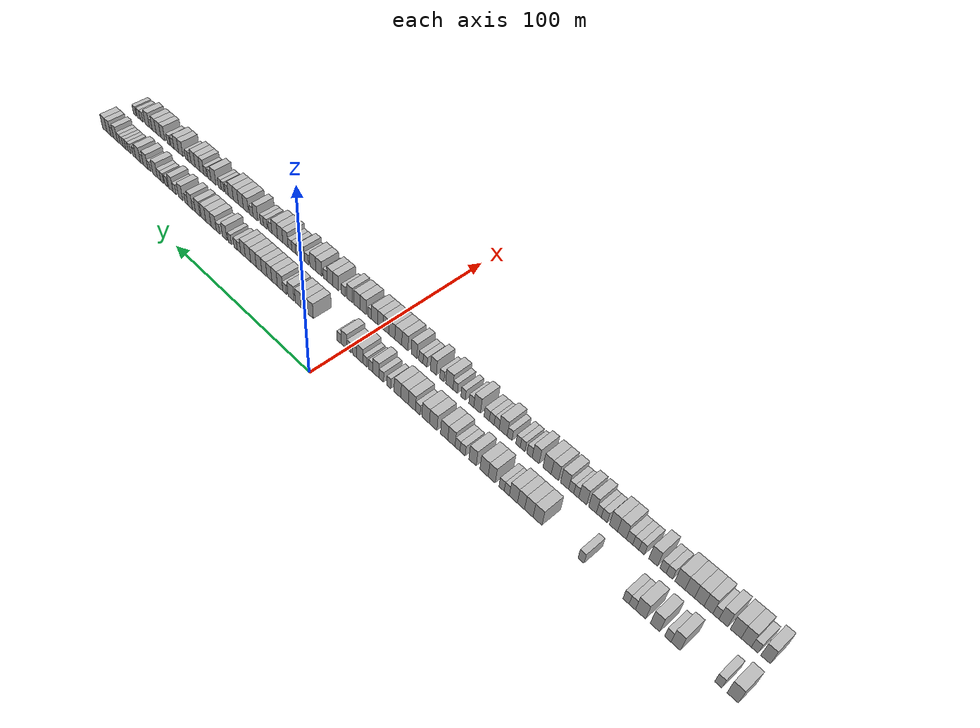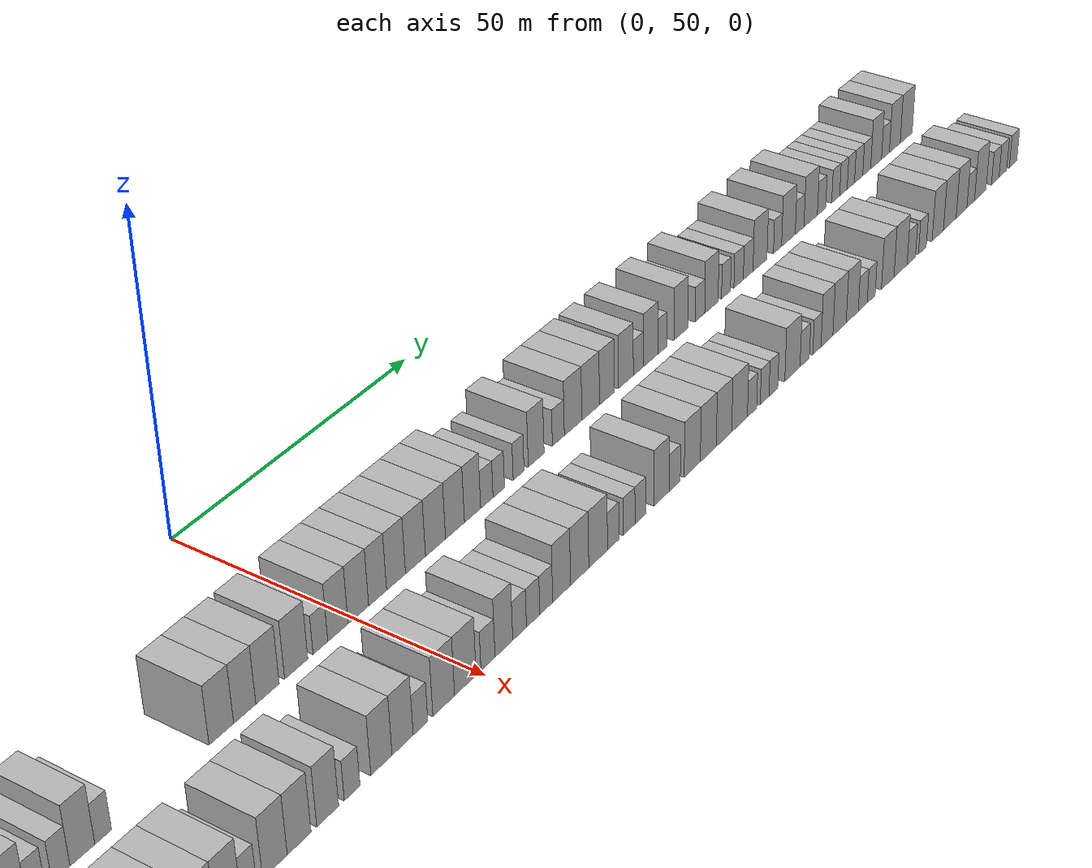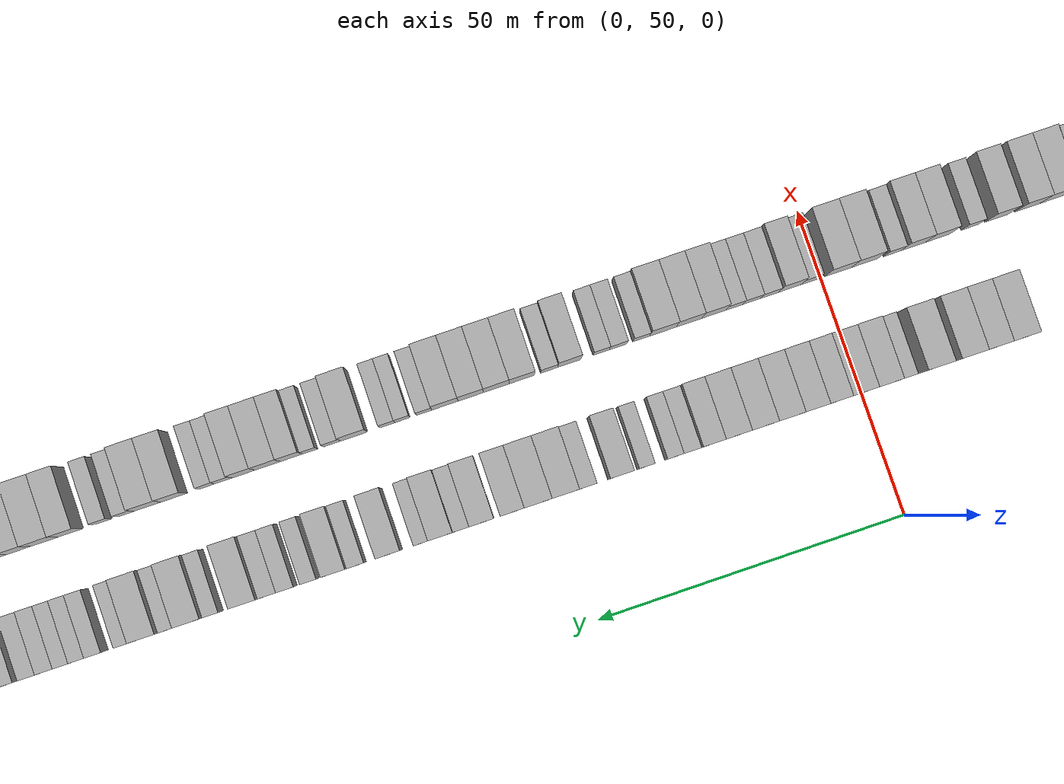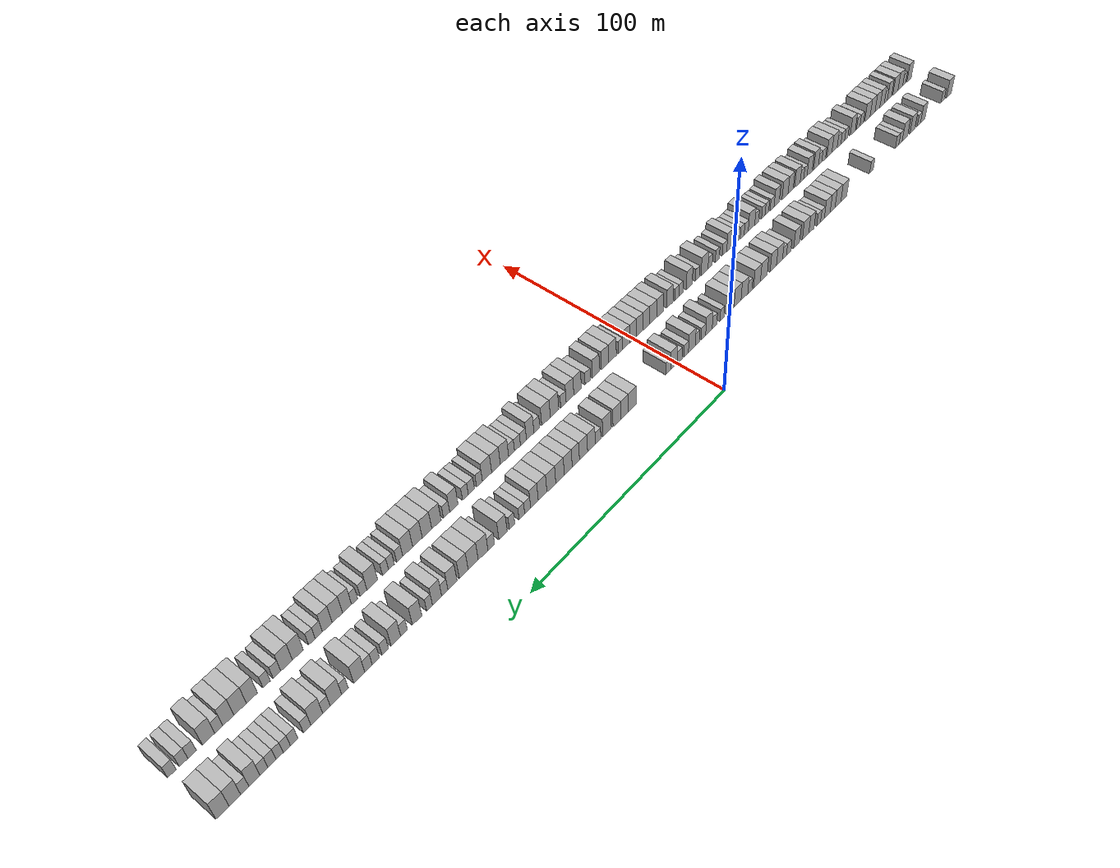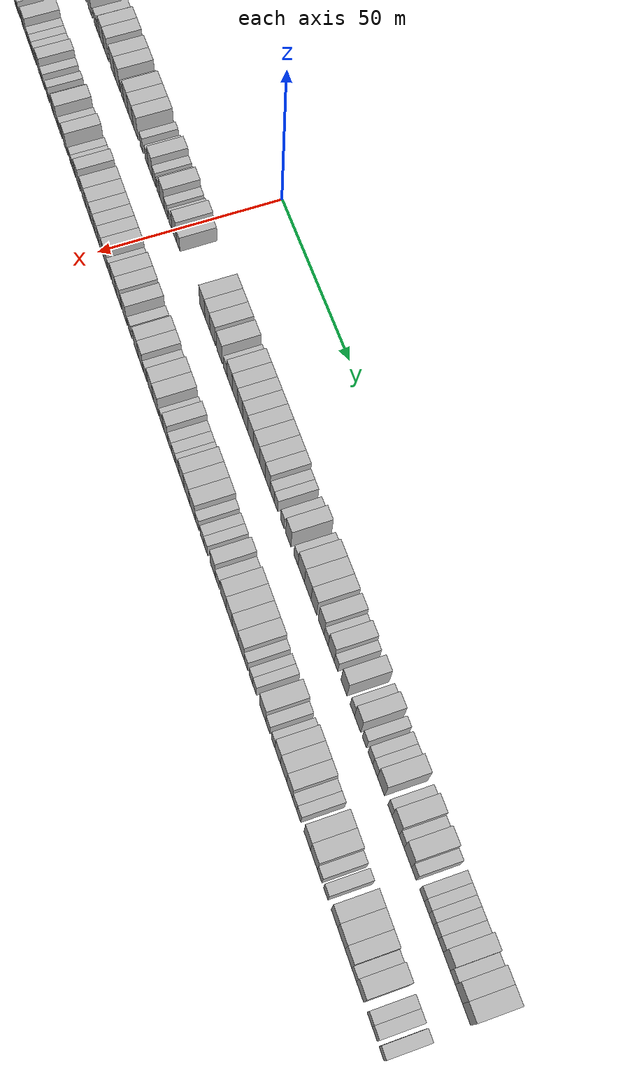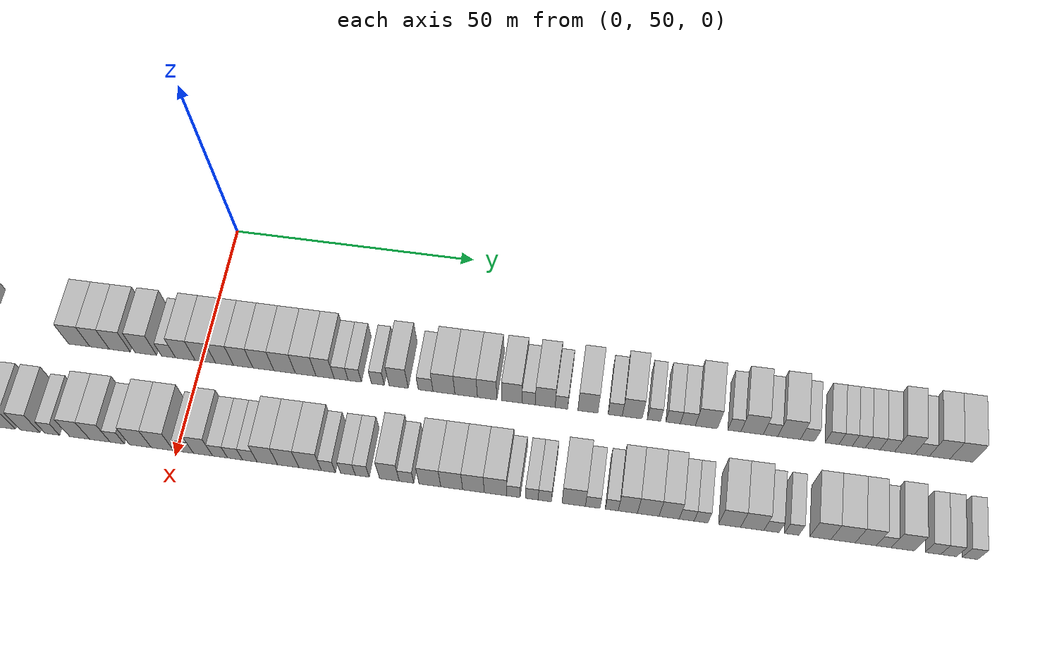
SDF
<sdf version="1.6">
 <world name="default">
  <scene>
   <sky><clouds><speed>12</speed></clouds></sky>
   <ambient>0.4 0.4 0.4 1</ambient>
   <background>0.7 0.7 0.7 1</background>
   <shadows>1</shadows>
  </scene>
  <gravity>0 0 -9.8066</gravity>
  <magnetic_field>6e-06 2.3e-05 -4.2e-05</magnetic_field>
  <physics default="0" name="default_physics" type="ode">
   <ode>
    <solver>
     <type>quick</type>
     <iters>10</iters>
     <sor>1.0</sor>
     <use_dynamic_moi_rescaling>0</use_dynamic_moi_rescaling>
    </solver>
    <constraints>
     <cfm>0</cfm>
     <erp>0.2</erp>
     <contact_max_correcting_vel>100</contact_max_correcting_vel>
     <contact_surface_layer>0.001</contact_surface_layer>
    </constraints>
   </ode>
   <max_step_size>0.004</max_step_size>
   <real_time_factor>1</real_time_factor>
   <real_time_update_rate>250</real_time_update_rate>
  </physics>
  <light name="sun" type="directional">
   <pose>0 0 10 0 0 0</pose>
   <diffuse>0.8 0.8 0.8 1</diffuse>
   <specular>0.2 0.2 0.2 1</specular>
   <attenuation>
    <range>1000</range>
    <constant>0.9</constant>
    <linear>0.01</linear>
    <quadratic>0.001</quadratic>
   </attenuation>
   <direction>-0.5 0.1 -0.9</direction>
  </light>
  <model name="building_1">
   <static>1</static>
   <pose>25.0000 -195.7773 0 0.000000 0.000000 0.000000</pose>
   <link name="link">
    <pose>0 0 4.50 0 0 0</pose>
    <collision name="collision"><geometry><box><size>10.0000 4.4454 9.0000</size></box></geometry></collision>
    <visual name="visual">
     <cast_shadows>0</cast_shadows>
     <geometry><box><size>10.0000 4.4454 9.0000</size></box></geometry>
     <material>
      <script>
       <uri>model://HANNAS_wall/materials/scripts</uri>
       <uri>model://HANNAS_wall/materials/textures</uri>
       <name>vrc/HANNAS_wall</name>
      </script>
     </material>
    </visual>
   </link>
  </model>
  <model name="building_2">
   <static>1</static>
   <pose>25.0000 -190.1237 0 0.000000 0.000000 0.000000</pose>
   <link name="link">
    <pose>0 0 3.00 0 0 0</pose>
    <collision name="collision"><geometry><box><size>10.0000 2.8618 6.0000</size></box></geometry></collision>
    <visual name="visual">
     <cast_shadows>0</cast_shadows>
     <geometry><box><size>10.0000 2.8618 6.0000</size></box></geometry>
     <material>
      <script>
       <uri>model://HANNAS_wall/materials/scripts</uri>
       <uri>model://HANNAS_wall/materials/textures</uri>
       <name>vrc/HANNAS_wall</name>
      </script>
     </material>
    </visual>
   </link>
  </model>
  <model name="building_3">
   <static>1</static>
   <pose>25.0000 -172.8571 0 0.000000 0.000000 0.000000</pose>
   <link name="link">
    <pose>0 0 4.50 0 0 0</pose>
    <collision name="collision"><geometry><box><size>10.0000 3.8905 9.0000</size></box></geometry></collision>
    <visual name="visual">
     <cast_shadows>0</cast_shadows>
     <geometry><box><size>10.0000 3.8905 9.0000</size></box></geometry>
     <material>
      <script>
       <uri>model://HANNAS_wall/materials/scripts</uri>
       <uri>model://HANNAS_wall/materials/textures</uri>
       <name>vrc/HANNAS_wall</name>
      </script>
     </material>
    </visual>
   </link>
  </model>
  <model name="building_4">
   <static>1</static>
   <pose>25.0000 -169.5295 0 0.000000 0.000000 0.000000</pose>
   <link name="link">
    <pose>0 0 3.00 0 0 0</pose>
    <collision name="collision"><geometry><box><size>10.0000 2.7647 6.0000</size></box></geometry></collision>
    <visual name="visual">
     <cast_shadows>0</cast_shadows>
     <geometry><box><size>10.0000 2.7647 6.0000</size></box></geometry>
     <material>
      <script>
       <uri>model://HANNAS_wall/materials/scripts</uri>
       <uri>model://HANNAS_wall/materials/textures</uri>
       <name>vrc/HANNAS_wall</name>
      </script>
     </material>
    </visual>
   </link>
  </model>
  <model name="building_5">
   <static>1</static>
   <pose>25.0000 -164.1152 0 0.000000 0.000000 0.000000</pose>
   <link name="link">
    <pose>0 0 4.50 0 0 0</pose>
    <collision name="collision"><geometry><box><size>10.0000 4.0638 9.0000</size></box></geometry></collision>
    <visual name="visual">
     <cast_shadows>0</cast_shadows>
     <geometry><box><size>10.0000 4.0638 9.0000</size></box></geometry>
     <material>
      <script>
       <uri>model://HANNAS_wall/materials/scripts</uri>
       <uri>model://HANNAS_wall/materials/textures</uri>
       <name>vrc/HANNAS_wall</name>
      </script>
     </material>
    </visual>
   </link>
  </model>
  <model name="building_6">
   <static>1</static>
   <pose>25.0000 -157.8585 0 0.000000 0.000000 0.000000</pose>
   <link name="link">
    <pose>0 0 4.50 0 0 0</pose>
    <collision name="collision"><geometry><box><size>10.0000 4.4497 9.0000</size></box></geometry></collision>
    <visual name="visual">
     <cast_shadows>0</cast_shadows>
     <geometry><box><size>10.0000 4.4497 9.0000</size></box></geometry>
     <material>
      <script>
       <uri>model://HANNAS_wall/materials/scripts</uri>
       <uri>model://HANNAS_wall/materials/textures</uri>
       <name>vrc/HANNAS_wall</name>
      </script>
     </material>
    </visual>
   </link>
  </model>
  <model name="building_7">
   <static>1</static>
   <pose>25.0000 -154.2386 0 0.000000 0.000000 0.000000</pose>
   <link name="link">
    <pose>0 0 3.00 0 0 0</pose>
    <collision name="collision"><geometry><box><size>10.0000 2.7901 6.0000</size></box></geometry></collision>
    <visual name="visual">
     <cast_shadows>0</cast_shadows>
     <geometry><box><size>10.0000 2.7901 6.0000</size></box></geometry>
     <material>
      <script>
       <uri>model://HANNAS_wall/materials/scripts</uri>
       <uri>model://HANNAS_wall/materials/textures</uri>
       <name>vrc/HANNAS_wall</name>
      </script>
     </material>
    </visual>
   </link>
  </model>
  <model name="building_8">
   <static>1</static>
   <pose>25.0000 -151.4736 0 0.000000 0.000000 0.000000</pose>
   <link name="link">
    <pose>0 0 3.00 0 0 0</pose>
    <collision name="collision"><geometry><box><size>10.0000 2.7399 6.0000</size></box></geometry></collision>
    <visual name="visual">
     <cast_shadows>0</cast_shadows>
     <geometry><box><size>10.0000 2.7399 6.0000</size></box></geometry>
     <material>
      <script>
       <uri>model://HANNAS_wall/materials/scripts</uri>
       <uri>model://HANNAS_wall/materials/textures</uri>
       <name>vrc/HANNAS_wall</name>
      </script>
     </material>
    </visual>
   </link>
  </model>
  <model name="building_9">
   <static>1</static>
   <pose>25.0000 -130.8985 0 0.000000 0.000000 0.000000</pose>
   <link name="link">
    <pose>0 0 3.00 0 0 0</pose>
    <collision name="collision"><geometry><box><size>10.0000 2.8034 6.0000</size></box></geometry></collision>
    <visual name="visual">
     <cast_shadows>0</cast_shadows>
     <geometry><box><size>10.0000 2.8034 6.0000</size></box></geometry>
     <material>
      <script>
       <uri>model://HANNAS_wall/materials/scripts</uri>
       <uri>model://HANNAS_wall/materials/textures</uri>
       <name>vrc/HANNAS_wall</name>
      </script>
     </material>
    </visual>
   </link>
  </model>
  <model name="building_10">
   <static>1</static>
   <pose>25.0000 -109.7788 0 0.000000 0.000000 0.000000</pose>
   <link name="link">
    <pose>0 0 4.50 0 0 0</pose>
    <collision name="collision"><geometry><box><size>10.0000 4.4786 9.0000</size></box></geometry></collision>
    <visual name="visual">
     <cast_shadows>0</cast_shadows>
     <geometry><box><size>10.0000 4.4786 9.0000</size></box></geometry>
     <material>
      <script>
       <uri>model://HANNAS_wall/materials/scripts</uri>
       <uri>model://HANNAS_wall/materials/textures</uri>
       <name>vrc/HANNAS_wall</name>
      </script>
     </material>
    </visual>
   </link>
  </model>
  <model name="building_11">
   <static>1</static>
   <pose>25.0000 -105.3849 0 0.000000 0.000000 0.000000</pose>
   <link name="link">
    <pose>0 0 4.50 0 0 0</pose>
    <collision name="collision"><geometry><box><size>10.0000 4.3093 9.0000</size></box></geometry></collision>
    <visual name="visual">
     <cast_shadows>0</cast_shadows>
     <geometry><box><size>10.0000 4.3093 9.0000</size></box></geometry>
     <material>
      <script>
       <uri>model://HANNAS_wall/materials/scripts</uri>
       <uri>model://HANNAS_wall/materials/textures</uri>
       <name>vrc/HANNAS_wall</name>
      </script>
     </material>
    </visual>
   </link>
  </model>
  <model name="building_12">
   <static>1</static>
   <pose>25.0000 -101.4164 0 0.000000 0.000000 0.000000</pose>
   <link name="link">
    <pose>0 0 4.50 0 0 0</pose>
    <collision name="collision"><geometry><box><size>10.0000 3.6275 9.0000</size></box></geometry></collision>
    <visual name="visual">
     <cast_shadows>0</cast_shadows>
     <geometry><box><size>10.0000 3.6275 9.0000</size></box></geometry>
     <material>
      <script>
       <uri>model://HANNAS_wall/materials/scripts</uri>
       <uri>model://HANNAS_wall/materials/textures</uri>
       <name>vrc/HANNAS_wall</name>
      </script>
     </material>
    </visual>
   </link>
  </model>
  <model name="building_13">
   <static>1</static>
   <pose>25.0000 -97.5190 0 0.000000 0.000000 0.000000</pose>
   <link name="link">
    <pose>0 0 4.50 0 0 0</pose>
    <collision name="collision"><geometry><box><size>10.0000 4.1674 9.0000</size></box></geometry></collision>
    <visual name="visual">
     <cast_shadows>0</cast_shadows>
     <geometry><box><size>10.0000 4.1674 9.0000</size></box></geometry>
     <material>
      <script>
       <uri>model://HANNAS_wall/materials/scripts</uri>
       <uri>model://HANNAS_wall/materials/textures</uri>
       <name>vrc/HANNAS_wall</name>
      </script>
     </material>
    </visual>
   </link>
  </model>
  <model name="building_14">
   <static>1</static>
   <pose>25.0000 -94.0891 0 0.000000 0.000000 0.000000</pose>
   <link name="link">
    <pose>0 0 3.00 0 0 0</pose>
    <collision name="collision"><geometry><box><size>10.0000 2.6924 6.0000</size></box></geometry></collision>
    <visual name="visual">
     <cast_shadows>0</cast_shadows>
     <geometry><box><size>10.0000 2.6924 6.0000</size></box></geometry>
     <material>
      <script>
       <uri>model://HANNAS_wall/materials/scripts</uri>
       <uri>model://HANNAS_wall/materials/textures</uri>
       <name>vrc/HANNAS_wall</name>
      </script>
     </material>
    </visual>
   </link>
  </model>
  <model name="building_15">
   <static>1</static>
   <pose>25.0000 -91.3764 0 0.000000 0.000000 0.000000</pose>
   <link name="link">
    <pose>0 0 3.00 0 0 0</pose>
    <collision name="collision"><geometry><box><size>10.0000 2.7331 6.0000</size></box></geometry></collision>
    <visual name="visual">
     <cast_shadows>0</cast_shadows>
     <geometry><box><size>10.0000 2.7331 6.0000</size></box></geometry>
     <material>
      <script>
       <uri>model://HANNAS_wall/materials/scripts</uri>
       <uri>model://HANNAS_wall/materials/textures</uri>
       <name>vrc/HANNAS_wall</name>
      </script>
     </material>
    </visual>
   </link>
  </model>
  <model name="building_16">
   <static>1</static>
   <pose>25.0000 -86.1300 0 0.000000 0.000000 0.000000</pose>
   <link name="link">
    <pose>0 0 4.50 0 0 0</pose>
    <collision name="collision"><geometry><box><size>10.0000 3.7596 9.0000</size></box></geometry></collision>
    <visual name="visual">
     <cast_shadows>0</cast_shadows>
     <geometry><box><size>10.0000 3.7596 9.0000</size></box></geometry>
     <material>
      <script>
       <uri>model://HANNAS_wall/materials/scripts</uri>
       <uri>model://HANNAS_wall/materials/textures</uri>
       <name>vrc/HANNAS_wall</name>
      </script>
     </material>
    </visual>
   </link>
  </model>
  <model name="building_17">
   <static>1</static>
   <pose>25.0000 -82.0215 0 0.000000 0.000000 0.000000</pose>
   <link name="link">
    <pose>0 0 4.50 0 0 0</pose>
    <collision name="collision"><geometry><box><size>10.0000 4.4574 9.0000</size></box></geometry></collision>
    <visual name="visual">
     <cast_shadows>0</cast_shadows>
     <geometry><box><size>10.0000 4.4574 9.0000</size></box></geometry>
     <material>
      <script>
       <uri>model://HANNAS_wall/materials/scripts</uri>
       <uri>model://HANNAS_wall/materials/textures</uri>
       <name>vrc/HANNAS_wall</name>
      </script>
     </material>
    </visual>
   </link>
  </model>
  <model name="building_18">
   <static>1</static>
   <pose>25.0000 -75.7765 0 0.000000 0.000000 0.000000</pose>
   <link name="link">
    <pose>0 0 4.50 0 0 0</pose>
    <collision name="collision"><geometry><box><size>10.0000 4.0327 9.0000</size></box></geometry></collision>
    <visual name="visual">
     <cast_shadows>0</cast_shadows>
     <geometry><box><size>10.0000 4.0327 9.0000</size></box></geometry>
     <material>
      <script>
       <uri>model://HANNAS_wall/materials/scripts</uri>
       <uri>model://HANNAS_wall/materials/textures</uri>
       <name>vrc/HANNAS_wall</name>
      </script>
     </material>
    </visual>
   </link>
  </model>
  <model name="building_19">
   <static>1</static>
   <pose>25.0000 -70.2856 0 0.000000 0.000000 0.000000</pose>
   <link name="link">
    <pose>0 0 3.00 0 0 0</pose>
    <collision name="collision"><geometry><box><size>10.0000 2.9492 6.0000</size></box></geometry></collision>
    <visual name="visual">
     <cast_shadows>0</cast_shadows>
     <geometry><box><size>10.0000 2.9492 6.0000</size></box></geometry>
     <material>
      <script>
       <uri>model://HANNAS_wall/materials/scripts</uri>
       <uri>model://HANNAS_wall/materials/textures</uri>
       <name>vrc/HANNAS_wall</name>
      </script>
     </material>
    </visual>
   </link>
  </model>
  <model name="building_20">
   <static>1</static>
   <pose>25.0000 -67.4418 0 0.000000 0.000000 0.000000</pose>
   <link name="link">
    <pose>0 0 3.00 0 0 0</pose>
    <collision name="collision"><geometry><box><size>10.0000 2.7383 6.0000</size></box></geometry></collision>
    <visual name="visual">
     <cast_shadows>0</cast_shadows>
     <geometry><box><size>10.0000 2.7383 6.0000</size></box></geometry>
     <material>
      <script>
       <uri>model://HANNAS_wall/materials/scripts</uri>
       <uri>model://HANNAS_wall/materials/textures</uri>
       <name>vrc/HANNAS_wall</name>
      </script>
     </material>
    </visual>
   </link>
  </model>
  <model name="building_21">
   <static>1</static>
   <pose>25.0000 -64.0328 0 0.000000 0.000000 0.000000</pose>
   <link name="link">
    <pose>0 0 4.50 0 0 0</pose>
    <collision name="collision"><geometry><box><size>10.0000 4.0797 9.0000</size></box></geometry></collision>
    <visual name="visual">
     <cast_shadows>0</cast_shadows>
     <geometry><box><size>10.0000 4.0797 9.0000</size></box></geometry>
     <material>
      <script>
       <uri>model://HANNAS_wall/materials/scripts</uri>
       <uri>model://HANNAS_wall/materials/textures</uri>
       <name>vrc/HANNAS_wall</name>
      </script>
     </material>
    </visual>
   </link>
  </model>
  <model name="building_22">
   <static>1</static>
   <pose>25.0000 -59.8915 0 0.000000 0.000000 0.000000</pose>
   <link name="link">
    <pose>0 0 4.50 0 0 0</pose>
    <collision name="collision"><geometry><box><size>10.0000 4.2029 9.0000</size></box></geometry></collision>
    <visual name="visual">
     <cast_shadows>0</cast_shadows>
     <geometry><box><size>10.0000 4.2029 9.0000</size></box></geometry>
     <material>
      <script>
       <uri>model://HANNAS_wall/materials/scripts</uri>
       <uri>model://HANNAS_wall/materials/textures</uri>
       <name>vrc/HANNAS_wall</name>
      </script>
     </material>
    </visual>
   </link>
  </model>
  <model name="building_23">
   <static>1</static>
   <pose>25.0000 -53.5899 0 0.000000 0.000000 0.000000</pose>
   <link name="link">
    <pose>0 0 4.50 0 0 0</pose>
    <collision name="collision"><geometry><box><size>10.0000 4.4005 9.0000</size></box></geometry></collision>
    <visual name="visual">
     <cast_shadows>0</cast_shadows>
     <geometry><box><size>10.0000 4.4005 9.0000</size></box></geometry>
     <material>
      <script>
       <uri>model://HANNAS_wall/materials/scripts</uri>
       <uri>model://HANNAS_wall/materials/textures</uri>
       <name>vrc/HANNAS_wall</name>
      </script>
     </material>
    </visual>
   </link>
  </model>
  <model name="building_24">
   <static>1</static>
   <pose>25.0000 -49.1624 0 0.000000 0.000000 0.000000</pose>
   <link name="link">
    <pose>0 0 4.50 0 0 0</pose>
    <collision name="collision"><geometry><box><size>10.0000 4.4544 9.0000</size></box></geometry></collision>
    <visual name="visual">
     <cast_shadows>0</cast_shadows>
     <geometry><box><size>10.0000 4.4544 9.0000</size></box></geometry>
     <material>
      <script>
       <uri>model://HANNAS_wall/materials/scripts</uri>
       <uri>model://HANNAS_wall/materials/textures</uri>
       <name>vrc/HANNAS_wall</name>
      </script>
     </material>
    </visual>
   </link>
  </model>
  <model name="building_25">
   <static>1</static>
   <pose>25.0000 -44.5468 0 0.000000 0.000000 0.000000</pose>
   <link name="link">
    <pose>0 0 3.00 0 0 0</pose>
    <collision name="collision"><geometry><box><size>10.0000 2.7766 6.0000</size></box></geometry></collision>
    <visual name="visual">
     <cast_shadows>0</cast_shadows>
     <geometry><box><size>10.0000 2.7766 6.0000</size></box></geometry>
     <material>
      <script>
       <uri>model://HANNAS_wall/materials/scripts</uri>
       <uri>model://HANNAS_wall/materials/textures</uri>
       <name>vrc/HANNAS_wall</name>
      </script>
     </material>
    </visual>
   </link>
  </model>
  <model name="building_26">
   <static>1</static>
   <pose>25.0000 -41.0109 0 0.000000 0.000000 0.000000</pose>
   <link name="link">
    <pose>0 0 4.50 0 0 0</pose>
    <collision name="collision"><geometry><box><size>10.0000 4.2952 9.0000</size></box></geometry></collision>
    <visual name="visual">
     <cast_shadows>0</cast_shadows>
     <geometry><box><size>10.0000 4.2952 9.0000</size></box></geometry>
     <material>
      <script>
       <uri>model://HANNAS_wall/materials/scripts</uri>
       <uri>model://HANNAS_wall/materials/textures</uri>
       <name>vrc/HANNAS_wall</name>
      </script>
     </material>
    </visual>
   </link>
  </model>
  <model name="building_27">
   <static>1</static>
   <pose>25.0000 -36.6326 0 0.000000 0.000000 0.000000</pose>
   <link name="link">
    <pose>0 0 4.50 0 0 0</pose>
    <collision name="collision"><geometry><box><size>10.0000 4.4614 9.0000</size></box></geometry></collision>
    <visual name="visual">
     <cast_shadows>0</cast_shadows>
     <geometry><box><size>10.0000 4.4614 9.0000</size></box></geometry>
     <material>
      <script>
       <uri>model://HANNAS_wall/materials/scripts</uri>
       <uri>model://HANNAS_wall/materials/textures</uri>
       <name>vrc/HANNAS_wall</name>
      </script>
     </material>
    </visual>
   </link>
  </model>
  <model name="building_28">
   <static>1</static>
   <pose>25.0000 -32.2918 0 0.000000 0.000000 0.000000</pose>
   <link name="link">
    <pose>0 0 4.50 0 0 0</pose>
    <collision name="collision"><geometry><box><size>10.0000 4.2203 9.0000</size></box></geometry></collision>
    <visual name="visual">
     <cast_shadows>0</cast_shadows>
     <geometry><box><size>10.0000 4.2203 9.0000</size></box></geometry>
     <material>
      <script>
       <uri>model://HANNAS_wall/materials/scripts</uri>
       <uri>model://HANNAS_wall/materials/textures</uri>
       <name>vrc/HANNAS_wall</name>
      </script>
     </material>
    </visual>
   </link>
  </model>
  <model name="building_29">
   <static>1</static>
   <pose>25.0000 -26.9423 0 0.000000 0.000000 0.000000</pose>
   <link name="link">
    <pose>0 0 3.00 0 0 0</pose>
    <collision name="collision"><geometry><box><size>10.0000 2.4787 6.0000</size></box></geometry></collision>
    <visual name="visual">
     <cast_shadows>0</cast_shadows>
     <geometry><box><size>10.0000 2.4787 6.0000</size></box></geometry>
     <material>
      <script>
       <uri>model://HANNAS_wall/materials/scripts</uri>
       <uri>model://HANNAS_wall/materials/textures</uri>
       <name>vrc/HANNAS_wall</name>
      </script>
     </material>
    </visual>
   </link>
  </model>
  <model name="building_30">
   <static>1</static>
   <pose>25.0000 -22.2968 0 0.000000 0.000000 0.000000</pose>
   <link name="link">
    <pose>0 0 3.00 0 0 0</pose>
    <collision name="collision"><geometry><box><size>10.0000 2.8123 6.0000</size></box></geometry></collision>
    <visual name="visual">
     <cast_shadows>0</cast_shadows>
     <geometry><box><size>10.0000 2.8123 6.0000</size></box></geometry>
     <material>
      <script>
       <uri>model://HANNAS_wall/materials/scripts</uri>
       <uri>model://HANNAS_wall/materials/textures</uri>
       <name>vrc/HANNAS_wall</name>
      </script>
     </material>
    </visual>
   </link>
  </model>
  <model name="building_31">
   <static>1</static>
   <pose>25.0000 -18.8963 0 0.000000 0.000000 0.000000</pose>
   <link name="link">
    <pose>0 0 4.50 0 0 0</pose>
    <collision name="collision"><geometry><box><size>10.0000 3.9886 9.0000</size></box></geometry></collision>
    <visual name="visual">
     <cast_shadows>0</cast_shadows>
     <geometry><box><size>10.0000 3.9886 9.0000</size></box></geometry>
     <material>
      <script>
       <uri>model://HANNAS_wall/materials/scripts</uri>
       <uri>model://HANNAS_wall/materials/textures</uri>
       <name>vrc/HANNAS_wall</name>
      </script>
     </material>
    </visual>
   </link>
  </model>
  <model name="building_32">
   <static>1</static>
   <pose>25.0000 -15.5508 0 0.000000 0.000000 0.000000</pose>
   <link name="link">
    <pose>0 0 3.00 0 0 0</pose>
    <collision name="collision"><geometry><box><size>10.0000 2.7024 6.0000</size></box></geometry></collision>
    <visual name="visual">
     <cast_shadows>0</cast_shadows>
     <geometry><box><size>10.0000 2.7024 6.0000</size></box></geometry>
     <material>
      <script>
       <uri>model://HANNAS_wall/materials/scripts</uri>
       <uri>model://HANNAS_wall/materials/textures</uri>
       <name>vrc/HANNAS_wall</name>
      </script>
     </material>
    </visual>
   </link>
  </model>
  <model name="building_33">
   <static>1</static>
   <pose>25.0000 -11.9756 0 0.000000 0.000000 0.000000</pose>
   <link name="link">
    <pose>0 0 3.00 0 0 0</pose>
    <collision name="collision"><geometry><box><size>10.0000 2.4482 6.0000</size></box></geometry></collision>
    <visual name="visual">
     <cast_shadows>0</cast_shadows>
     <geometry><box><size>10.0000 2.4482 6.0000</size></box></geometry>
     <material>
      <script>
       <uri>model://HANNAS_wall/materials/scripts</uri>
       <uri>model://HANNAS_wall/materials/textures</uri>
       <name>vrc/HANNAS_wall</name>
      </script>
     </material>
    </visual>
   </link>
  </model>
  <model name="building_34">
   <static>1</static>
   <pose>25.0000 -8.6893 0 0.000000 0.000000 0.000000</pose>
   <link name="link">
    <pose>0 0 4.50 0 0 0</pose>
    <collision name="collision"><geometry><box><size>10.0000 4.1243 9.0000</size></box></geometry></collision>
    <visual name="visual">
     <cast_shadows>0</cast_shadows>
     <geometry><box><size>10.0000 4.1243 9.0000</size></box></geometry>
     <material>
      <script>
       <uri>model://HANNAS_wall/materials/scripts</uri>
       <uri>model://HANNAS_wall/materials/textures</uri>
       <name>vrc/HANNAS_wall</name>
      </script>
     </material>
    </visual>
   </link>
  </model>
  <model name="building_35">
   <static>1</static>
   <pose>25.0000 -5.2549 0 0.000000 0.000000 0.000000</pose>
   <link name="link">
    <pose>0 0 3.00 0 0 0</pose>
    <collision name="collision"><geometry><box><size>10.0000 2.7446 6.0000</size></box></geometry></collision>
    <visual name="visual">
     <cast_shadows>0</cast_shadows>
     <geometry><box><size>10.0000 2.7446 6.0000</size></box></geometry>
     <material>
      <script>
       <uri>model://HANNAS_wall/materials/scripts</uri>
       <uri>model://HANNAS_wall/materials/textures</uri>
       <name>vrc/HANNAS_wall</name>
      </script>
     </material>
    </visual>
   </link>
  </model>
  <model name="building_36">
   <static>1</static>
   <pose>25.0000 -1.4913 0 0.000000 0.000000 0.000000</pose>
   <link name="link">
    <pose>0 0 3.00 0 0 0</pose>
    <collision name="collision"><geometry><box><size>10.0000 2.7827 6.0000</size></box></geometry></collision>
    <visual name="visual">
     <cast_shadows>0</cast_shadows>
     <geometry><box><size>10.0000 2.7827 6.0000</size></box></geometry>
     <material>
      <script>
       <uri>model://HANNAS_wall/materials/scripts</uri>
       <uri>model://HANNAS_wall/materials/textures</uri>
       <name>vrc/HANNAS_wall</name>
      </script>
     </material>
    </visual>
   </link>
  </model>
  <model name="building_37">
   <static>1</static>
   <pose>25.0000 1.8488 0 0.000000 0.000000 0.000000</pose>
   <link name="link">
    <pose>0 0 4.50 0 0 0</pose>
    <collision name="collision"><geometry><box><size>10.0000 3.8975 9.0000</size></box></geometry></collision>
    <visual name="visual">
     <cast_shadows>0</cast_shadows>
     <geometry><box><size>10.0000 3.8975 9.0000</size></box></geometry>
     <material>
      <script>
       <uri>model://HANNAS_wall/materials/scripts</uri>
       <uri>model://HANNAS_wall/materials/textures</uri>
       <name>vrc/HANNAS_wall</name>
      </script>
     </material>
    </visual>
   </link>
  </model>
  <model name="building_38">
   <static>1</static>
   <pose>25.0000 5.1335 0 0.000000 0.000000 0.000000</pose>
   <link name="link">
    <pose>0 0 3.00 0 0 0</pose>
    <collision name="collision"><geometry><box><size>10.0000 2.6717 6.0000</size></box></geometry></collision>
    <visual name="visual">
     <cast_shadows>0</cast_shadows>
     <geometry><box><size>10.0000 2.6717 6.0000</size></box></geometry>
     <material>
      <script>
       <uri>model://HANNAS_wall/materials/scripts</uri>
       <uri>model://HANNAS_wall/materials/textures</uri>
       <name>vrc/HANNAS_wall</name>
      </script>
     </material>
    </visual>
   </link>
  </model>
  <model name="building_39">
   <static>1</static>
   <pose>25.0000 25.0117 0 0.000000 0.000000 0.000000</pose>
   <link name="link">
    <pose>0 0 4.50 0 0 0</pose>
    <collision name="collision"><geometry><box><size>10.0000 4.3616 9.0000</size></box></geometry></collision>
    <visual name="visual">
     <cast_shadows>0</cast_shadows>
     <geometry><box><size>10.0000 4.3616 9.0000</size></box></geometry>
     <material>
      <script>
       <uri>model://HANNAS_wall/materials/scripts</uri>
       <uri>model://HANNAS_wall/materials/textures</uri>
       <name>vrc/HANNAS_wall</name>
      </script>
     </material>
    </visual>
   </link>
  </model>
  <model name="building_40">
   <static>1</static>
   <pose>25.0000 29.1984 0 0.000000 0.000000 0.000000</pose>
   <link name="link">
    <pose>0 0 4.50 0 0 0</pose>
    <collision name="collision"><geometry><box><size>10.0000 4.0117 9.0000</size></box></geometry></collision>
    <visual name="visual">
     <cast_shadows>0</cast_shadows>
     <geometry><box><size>10.0000 4.0117 9.0000</size></box></geometry>
     <material>
      <script>
       <uri>model://HANNAS_wall/materials/scripts</uri>
       <uri>model://HANNAS_wall/materials/textures</uri>
       <name>vrc/HANNAS_wall</name>
      </script>
     </material>
    </visual>
   </link>
  </model>
  <model name="building_41">
   <static>1</static>
   <pose>25.0000 33.3631 0 0.000000 0.000000 0.000000</pose>
   <link name="link">
    <pose>0 0 4.50 0 0 0</pose>
    <collision name="collision"><geometry><box><size>10.0000 4.3178 9.0000</size></box></geometry></collision>
    <visual name="visual">
     <cast_shadows>0</cast_shadows>
     <geometry><box><size>10.0000 4.3178 9.0000</size></box></geometry>
     <material>
      <script>
       <uri>model://HANNAS_wall/materials/scripts</uri>
       <uri>model://HANNAS_wall/materials/textures</uri>
       <name>vrc/HANNAS_wall</name>
      </script>
     </material>
    </visual>
   </link>
  </model>
  <model name="building_42">
   <static>1</static>
   <pose>25.0000 38.7212 0 0.000000 0.000000 0.000000</pose>
   <link name="link">
    <pose>0 0 4.50 0 0 0</pose>
    <collision name="collision"><geometry><box><size>10.0000 4.3984 9.0000</size></box></geometry></collision>
    <visual name="visual">
     <cast_shadows>0</cast_shadows>
     <geometry><box><size>10.0000 4.3984 9.0000</size></box></geometry>
     <material>
      <script>
       <uri>model://HANNAS_wall/materials/scripts</uri>
       <uri>model://HANNAS_wall/materials/textures</uri>
       <name>vrc/HANNAS_wall</name>
      </script>
     </material>
    </visual>
   </link>
  </model>
  <model name="building_43">
   <static>1</static>
   <pose>25.0000 43.3477 0 0.000000 0.000000 0.000000</pose>
   <link name="link">
    <pose>0 0 3.00 0 0 0</pose>
    <collision name="collision"><geometry><box><size>10.0000 2.8546 6.0000</size></box></geometry></collision>
    <visual name="visual">
     <cast_shadows>0</cast_shadows>
     <geometry><box><size>10.0000 2.8546 6.0000</size></box></geometry>
     <material>
      <script>
       <uri>model://HANNAS_wall/materials/scripts</uri>
       <uri>model://HANNAS_wall/materials/textures</uri>
       <name>vrc/HANNAS_wall</name>
      </script>
     </material>
    </visual>
   </link>
  </model>
  <model name="building_44">
   <static>1</static>
   <pose>25.0000 46.7679 0 0.000000 0.000000 0.000000</pose>
   <link name="link">
    <pose>0 0 4.50 0 0 0</pose>
    <collision name="collision"><geometry><box><size>10.0000 3.9857 9.0000</size></box></geometry></collision>
    <visual name="visual">
     <cast_shadows>0</cast_shadows>
     <geometry><box><size>10.0000 3.9857 9.0000</size></box></geometry>
     <material>
      <script>
       <uri>model://HANNAS_wall/materials/scripts</uri>
       <uri>model://HANNAS_wall/materials/textures</uri>
       <name>vrc/HANNAS_wall</name>
      </script>
     </material>
    </visual>
   </link>
  </model>
  <model name="building_45">
   <static>1</static>
   <pose>25.0000 50.8292 0 0.000000 0.000000 0.000000</pose>
   <link name="link">
    <pose>0 0 4.50 0 0 0</pose>
    <collision name="collision"><geometry><box><size>10.0000 4.1369 9.0000</size></box></geometry></collision>
    <visual name="visual">
     <cast_shadows>0</cast_shadows>
     <geometry><box><size>10.0000 4.1369 9.0000</size></box></geometry>
     <material>
      <script>
       <uri>model://HANNAS_wall/materials/scripts</uri>
       <uri>model://HANNAS_wall/materials/textures</uri>
       <name>vrc/HANNAS_wall</name>
      </script>
     </material>
    </visual>
   </link>
  </model>
  <model name="building_46">
   <static>1</static>
   <pose>25.0000 54.7279 0 0.000000 0.000000 0.000000</pose>
   <link name="link">
    <pose>0 0 4.50 0 0 0</pose>
    <collision name="collision"><geometry><box><size>10.0000 3.6604 9.0000</size></box></geometry></collision>
    <visual name="visual">
     <cast_shadows>0</cast_shadows>
     <geometry><box><size>10.0000 3.6604 9.0000</size></box></geometry>
     <material>
      <script>
       <uri>model://HANNAS_wall/materials/scripts</uri>
       <uri>model://HANNAS_wall/materials/textures</uri>
       <name>vrc/HANNAS_wall</name>
      </script>
     </material>
    </visual>
   </link>
  </model>
  <model name="building_47">
   <static>1</static>
   <pose>25.0000 58.5285 0 0.000000 0.000000 0.000000</pose>
   <link name="link">
    <pose>0 0 4.50 0 0 0</pose>
    <collision name="collision"><geometry><box><size>10.0000 3.9409 9.0000</size></box></geometry></collision>
    <visual name="visual">
     <cast_shadows>0</cast_shadows>
     <geometry><box><size>10.0000 3.9409 9.0000</size></box></geometry>
     <material>
      <script>
       <uri>model://HANNAS_wall/materials/scripts</uri>
       <uri>model://HANNAS_wall/materials/textures</uri>
       <name>vrc/HANNAS_wall</name>
      </script>
     </material>
    </visual>
   </link>
  </model>
  <model name="building_48">
   <static>1</static>
   <pose>25.0000 62.6112 0 0.000000 0.000000 0.000000</pose>
   <link name="link">
    <pose>0 0 4.50 0 0 0</pose>
    <collision name="collision"><geometry><box><size>10.0000 4.2244 9.0000</size></box></geometry></collision>
    <visual name="visual">
     <cast_shadows>0</cast_shadows>
     <geometry><box><size>10.0000 4.2244 9.0000</size></box></geometry>
     <material>
      <script>
       <uri>model://HANNAS_wall/materials/scripts</uri>
       <uri>model://HANNAS_wall/materials/textures</uri>
       <name>vrc/HANNAS_wall</name>
      </script>
     </material>
    </visual>
   </link>
  </model>
  <model name="building_49">
   <static>1</static>
   <pose>25.0000 66.8861 0 0.000000 0.000000 0.000000</pose>
   <link name="link">
    <pose>0 0 4.50 0 0 0</pose>
    <collision name="collision"><geometry><box><size>10.0000 4.3253 9.0000</size></box></geometry></collision>
    <visual name="visual">
     <cast_shadows>0</cast_shadows>
     <geometry><box><size>10.0000 4.3253 9.0000</size></box></geometry>
     <material>
      <script>
       <uri>model://HANNAS_wall/materials/scripts</uri>
       <uri>model://HANNAS_wall/materials/textures</uri>
       <name>vrc/HANNAS_wall</name>
      </script>
     </material>
    </visual>
   </link>
  </model>
  <model name="building_50">
   <static>1</static>
   <pose>25.0000 71.1344 0 0.000000 0.000000 0.000000</pose>
   <link name="link">
    <pose>0 0 4.50 0 0 0</pose>
    <collision name="collision"><geometry><box><size>10.0000 4.1714 9.0000</size></box></geometry></collision>
    <visual name="visual">
     <cast_shadows>0</cast_shadows>
     <geometry><box><size>10.0000 4.1714 9.0000</size></box></geometry>
     <material>
      <script>
       <uri>model://HANNAS_wall/materials/scripts</uri>
       <uri>model://HANNAS_wall/materials/textures</uri>
       <name>vrc/HANNAS_wall</name>
      </script>
     </material>
    </visual>
   </link>
  </model>
  <model name="building_51">
   <static>1</static>
   <pose>25.0000 75.0336 0 0.000000 0.000000 0.000000</pose>
   <link name="link">
    <pose>0 0 4.50 0 0 0</pose>
    <collision name="collision"><geometry><box><size>10.0000 3.6269 9.0000</size></box></geometry></collision>
    <visual name="visual">
     <cast_shadows>0</cast_shadows>
     <geometry><box><size>10.0000 3.6269 9.0000</size></box></geometry>
     <material>
      <script>
       <uri>model://HANNAS_wall/materials/scripts</uri>
       <uri>model://HANNAS_wall/materials/textures</uri>
       <name>vrc/HANNAS_wall</name>
      </script>
     </material>
    </visual>
   </link>
  </model>
  <model name="building_52">
   <static>1</static>
   <pose>25.0000 78.2536 0 0.000000 0.000000 0.000000</pose>
   <link name="link">
    <pose>0 0 3.00 0 0 0</pose>
    <collision name="collision"><geometry><box><size>10.0000 2.8131 6.0000</size></box></geometry></collision>
    <visual name="visual">
     <cast_shadows>0</cast_shadows>
     <geometry><box><size>10.0000 2.8131 6.0000</size></box></geometry>
     <material>
      <script>
       <uri>model://HANNAS_wall/materials/scripts</uri>
       <uri>model://HANNAS_wall/materials/textures</uri>
       <name>vrc/HANNAS_wall</name>
      </script>
     </material>
    </visual>
   </link>
  </model>
  <model name="building_53">
   <static>1</static>
   <pose>25.0000 80.9856 0 0.000000 0.000000 0.000000</pose>
   <link name="link">
    <pose>0 0 3.00 0 0 0</pose>
    <collision name="collision"><geometry><box><size>10.0000 2.6509 6.0000</size></box></geometry></collision>
    <visual name="visual">
     <cast_shadows>0</cast_shadows>
     <geometry><box><size>10.0000 2.6509 6.0000</size></box></geometry>
     <material>
      <script>
       <uri>model://HANNAS_wall/materials/scripts</uri>
       <uri>model://HANNAS_wall/materials/textures</uri>
       <name>vrc/HANNAS_wall</name>
      </script>
     </material>
    </visual>
   </link>
  </model>
  <model name="building_54">
   <static>1</static>
   <pose>25.0000 85.5860 0 0.000000 0.000000 0.000000</pose>
   <link name="link">
    <pose>0 0 3.00 0 0 0</pose>
    <collision name="collision"><geometry><box><size>10.0000 2.5500 6.0000</size></box></geometry></collision>
    <visual name="visual">
     <cast_shadows>0</cast_shadows>
     <geometry><box><size>10.0000 2.5500 6.0000</size></box></geometry>
     <material>
      <script>
       <uri>model://HANNAS_wall/materials/scripts</uri>
       <uri>model://HANNAS_wall/materials/textures</uri>
       <name>vrc/HANNAS_wall</name>
      </script>
     </material>
    </visual>
   </link>
  </model>
  <model name="building_55">
   <static>1</static>
   <pose>25.0000 89.7523 0 0.000000 0.000000 0.000000</pose>
   <link name="link">
    <pose>0 0 4.50 0 0 0</pose>
    <collision name="collision"><geometry><box><size>10.0000 3.7826 9.0000</size></box></geometry></collision>
    <visual name="visual">
     <cast_shadows>0</cast_shadows>
     <geometry><box><size>10.0000 3.7826 9.0000</size></box></geometry>
     <material>
      <script>
       <uri>model://HANNAS_wall/materials/scripts</uri>
       <uri>model://HANNAS_wall/materials/textures</uri>
       <name>vrc/HANNAS_wall</name>
      </script>
     </material>
    </visual>
   </link>
  </model>
  <model name="building_56">
   <static>1</static>
   <pose>25.0000 95.1099 0 0.000000 0.000000 0.000000</pose>
   <link name="link">
    <pose>0 0 3.00 0 0 0</pose>
    <collision name="collision"><geometry><box><size>10.0000 2.9327 6.0000</size></box></geometry></collision>
    <visual name="visual">
     <cast_shadows>0</cast_shadows>
     <geometry><box><size>10.0000 2.9327 6.0000</size></box></geometry>
     <material>
      <script>
       <uri>model://HANNAS_wall/materials/scripts</uri>
       <uri>model://HANNAS_wall/materials/textures</uri>
       <name>vrc/HANNAS_wall</name>
      </script>
     </material>
    </visual>
   </link>
  </model>
  <model name="building_57">
   <static>1</static>
   <pose>25.0000 98.7507 0 0.000000 0.000000 0.000000</pose>
   <link name="link">
    <pose>0 0 4.50 0 0 0</pose>
    <collision name="collision"><geometry><box><size>10.0000 4.3488 9.0000</size></box></geometry></collision>
    <visual name="visual">
     <cast_shadows>0</cast_shadows>
     <geometry><box><size>10.0000 4.3488 9.0000</size></box></geometry>
     <material>
      <script>
       <uri>model://HANNAS_wall/materials/scripts</uri>
       <uri>model://HANNAS_wall/materials/textures</uri>
       <name>vrc/HANNAS_wall</name>
      </script>
     </material>
    </visual>
   </link>
  </model>
  <model name="building_58">
   <static>1</static>
   <pose>25.0000 103.1546 0 0.000000 0.000000 0.000000</pose>
   <link name="link">
    <pose>0 0 4.50 0 0 0</pose>
    <collision name="collision"><geometry><box><size>10.0000 4.4590 9.0000</size></box></geometry></collision>
    <visual name="visual">
     <cast_shadows>0</cast_shadows>
     <geometry><box><size>10.0000 4.4590 9.0000</size></box></geometry>
     <material>
      <script>
       <uri>model://HANNAS_wall/materials/scripts</uri>
       <uri>model://HANNAS_wall/materials/textures</uri>
       <name>vrc/HANNAS_wall</name>
      </script>
     </material>
    </visual>
   </link>
  </model>
  <model name="building_59">
   <static>1</static>
   <pose>25.0000 107.3013 0 0.000000 0.000000 0.000000</pose>
   <link name="link">
    <pose>0 0 4.50 0 0 0</pose>
    <collision name="collision"><geometry><box><size>10.0000 3.8344 9.0000</size></box></geometry></collision>
    <visual name="visual">
     <cast_shadows>0</cast_shadows>
     <geometry><box><size>10.0000 3.8344 9.0000</size></box></geometry>
     <material>
      <script>
       <uri>model://HANNAS_wall/materials/scripts</uri>
       <uri>model://HANNAS_wall/materials/textures</uri>
       <name>vrc/HANNAS_wall</name>
      </script>
     </material>
    </visual>
   </link>
  </model>
  <model name="building_60">
   <static>1</static>
   <pose>25.0000 112.1923 0 0.000000 0.000000 0.000000</pose>
   <link name="link">
    <pose>0 0 4.50 0 0 0</pose>
    <collision name="collision"><geometry><box><size>10.0000 3.9476 9.0000</size></box></geometry></collision>
    <visual name="visual">
     <cast_shadows>0</cast_shadows>
     <geometry><box><size>10.0000 3.9476 9.0000</size></box></geometry>
     <material>
      <script>
       <uri>model://HANNAS_wall/materials/scripts</uri>
       <uri>model://HANNAS_wall/materials/textures</uri>
       <name>vrc/HANNAS_wall</name>
      </script>
     </material>
    </visual>
   </link>
  </model>
  <model name="building_61">
   <static>1</static>
   <pose>25.0000 115.4911 0 0.000000 0.000000 0.000000</pose>
   <link name="link">
    <pose>0 0 3.00 0 0 0</pose>
    <collision name="collision"><geometry><box><size>10.0000 2.6501 6.0000</size></box></geometry></collision>
    <visual name="visual">
     <cast_shadows>0</cast_shadows>
     <geometry><box><size>10.0000 2.6501 6.0000</size></box></geometry>
     <material>
      <script>
       <uri>model://HANNAS_wall/materials/scripts</uri>
       <uri>model://HANNAS_wall/materials/textures</uri>
       <name>vrc/HANNAS_wall</name>
      </script>
     </material>
    </visual>
   </link>
  </model>
  <model name="building_62">
   <static>1</static>
   <pose>25.0000 118.7586 0 0.000000 0.000000 0.000000</pose>
   <link name="link">
    <pose>0 0 4.50 0 0 0</pose>
    <collision name="collision"><geometry><box><size>10.0000 3.8848 9.0000</size></box></geometry></collision>
    <visual name="visual">
     <cast_shadows>0</cast_shadows>
     <geometry><box><size>10.0000 3.8848 9.0000</size></box></geometry>
     <material>
      <script>
       <uri>model://HANNAS_wall/materials/scripts</uri>
       <uri>model://HANNAS_wall/materials/textures</uri>
       <name>vrc/HANNAS_wall</name>
      </script>
     </material>
    </visual>
   </link>
  </model>
  <model name="building_63">
   <static>1</static>
   <pose>25.0000 121.9209 0 0.000000 0.000000 0.000000</pose>
   <link name="link">
    <pose>0 0 3.00 0 0 0</pose>
    <collision name="collision"><geometry><box><size>10.0000 2.4398 6.0000</size></box></geometry></collision>
    <visual name="visual">
     <cast_shadows>0</cast_shadows>
     <geometry><box><size>10.0000 2.4398 6.0000</size></box></geometry>
     <material>
      <script>
       <uri>model://HANNAS_wall/materials/scripts</uri>
       <uri>model://HANNAS_wall/materials/textures</uri>
       <name>vrc/HANNAS_wall</name>
      </script>
     </material>
    </visual>
   </link>
  </model>
  <model name="building_64">
   <static>1</static>
   <pose>25.0000 127.0968 0 0.000000 0.000000 0.000000</pose>
   <link name="link">
    <pose>0 0 4.50 0 0 0</pose>
    <collision name="collision"><geometry><box><size>10.0000 3.9120 9.0000</size></box></geometry></collision>
    <visual name="visual">
     <cast_shadows>0</cast_shadows>
     <geometry><box><size>10.0000 3.9120 9.0000</size></box></geometry>
     <material>
      <script>
       <uri>model://HANNAS_wall/materials/scripts</uri>
       <uri>model://HANNAS_wall/materials/textures</uri>
       <name>vrc/HANNAS_wall</name>
      </script>
     </material>
    </visual>
   </link>
  </model>
  <model name="building_65">
   <static>1</static>
   <pose>25.0000 132.4365 0 0.000000 0.000000 0.000000</pose>
   <link name="link">
    <pose>0 0 3.00 0 0 0</pose>
    <collision name="collision"><geometry><box><size>10.0000 2.7674 6.0000</size></box></geometry></collision>
    <visual name="visual">
     <cast_shadows>0</cast_shadows>
     <geometry><box><size>10.0000 2.7674 6.0000</size></box></geometry>
     <material>
      <script>
       <uri>model://HANNAS_wall/materials/scripts</uri>
       <uri>model://HANNAS_wall/materials/textures</uri>
       <name>vrc/HANNAS_wall</name>
      </script>
     </material>
    </visual>
   </link>
  </model>
  <model name="building_66">
   <static>1</static>
   <pose>25.0000 135.7534 0 0.000000 0.000000 0.000000</pose>
   <link name="link">
    <pose>0 0 4.50 0 0 0</pose>
    <collision name="collision"><geometry><box><size>10.0000 3.8664 9.0000</size></box></geometry></collision>
    <visual name="visual">
     <cast_shadows>0</cast_shadows>
     <geometry><box><size>10.0000 3.8664 9.0000</size></box></geometry>
     <material>
      <script>
       <uri>model://HANNAS_wall/materials/scripts</uri>
       <uri>model://HANNAS_wall/materials/textures</uri>
       <name>vrc/HANNAS_wall</name>
      </script>
     </material>
    </visual>
   </link>
  </model>
  <model name="building_67">
   <static>1</static>
   <pose>25.0000 139.9973 0 0.000000 0.000000 0.000000</pose>
   <link name="link">
    <pose>0 0 3.00 0 0 0</pose>
    <collision name="collision"><geometry><box><size>10.0000 2.6214 6.0000</size></box></geometry></collision>
    <visual name="visual">
     <cast_shadows>0</cast_shadows>
     <geometry><box><size>10.0000 2.6214 6.0000</size></box></geometry>
     <material>
      <script>
       <uri>model://HANNAS_wall/materials/scripts</uri>
       <uri>model://HANNAS_wall/materials/textures</uri>
       <name>vrc/HANNAS_wall</name>
      </script>
     </material>
    </visual>
   </link>
  </model>
  <model name="building_68">
   <static>1</static>
   <pose>25.0000 143.7185 0 0.000000 0.000000 0.000000</pose>
   <link name="link">
    <pose>0 0 3.00 0 0 0</pose>
    <collision name="collision"><geometry><box><size>10.0000 2.8210 6.0000</size></box></geometry></collision>
    <visual name="visual">
     <cast_shadows>0</cast_shadows>
     <geometry><box><size>10.0000 2.8210 6.0000</size></box></geometry>
     <material>
      <script>
       <uri>model://HANNAS_wall/materials/scripts</uri>
       <uri>model://HANNAS_wall/materials/textures</uri>
       <name>vrc/HANNAS_wall</name>
      </script>
     </material>
    </visual>
   </link>
  </model>
  <model name="building_69">
   <static>1</static>
   <pose>25.0000 146.5815 0 0.000000 0.000000 0.000000</pose>
   <link name="link">
    <pose>0 0 3.00 0 0 0</pose>
    <collision name="collision"><geometry><box><size>10.0000 2.9051 6.0000</size></box></geometry></collision>
    <visual name="visual">
     <cast_shadows>0</cast_shadows>
     <geometry><box><size>10.0000 2.9051 6.0000</size></box></geometry>
     <material>
      <script>
       <uri>model://HANNAS_wall/materials/scripts</uri>
       <uri>model://HANNAS_wall/materials/textures</uri>
       <name>vrc/HANNAS_wall</name>
      </script>
     </material>
    </visual>
   </link>
  </model>
  <model name="building_70">
   <static>1</static>
   <pose>25.0000 150.1681 0 0.000000 0.000000 0.000000</pose>
   <link name="link">
    <pose>0 0 4.50 0 0 0</pose>
    <collision name="collision"><geometry><box><size>10.0000 4.2681 9.0000</size></box></geometry></collision>
    <visual name="visual">
     <cast_shadows>0</cast_shadows>
     <geometry><box><size>10.0000 4.2681 9.0000</size></box></geometry>
     <material>
      <script>
       <uri>model://HANNAS_wall/materials/scripts</uri>
       <uri>model://HANNAS_wall/materials/textures</uri>
       <name>vrc/HANNAS_wall</name>
      </script>
     </material>
    </visual>
   </link>
  </model>
  <model name="building_71">
   <static>1</static>
   <pose>25.0000 155.5696 0 0.000000 0.000000 0.000000</pose>
   <link name="link">
    <pose>0 0 3.00 0 0 0</pose>
    <collision name="collision"><geometry><box><size>10.0000 2.5348 6.0000</size></box></geometry></collision>
    <visual name="visual">
     <cast_shadows>0</cast_shadows>
     <geometry><box><size>10.0000 2.5348 6.0000</size></box></geometry>
     <material>
      <script>
       <uri>model://HANNAS_wall/materials/scripts</uri>
       <uri>model://HANNAS_wall/materials/textures</uri>
       <name>vrc/HANNAS_wall</name>
      </script>
     </material>
    </visual>
   </link>
  </model>
  <model name="building_72">
   <static>1</static>
   <pose>25.0000 158.9892 0 0.000000 0.000000 0.000000</pose>
   <link name="link">
    <pose>0 0 4.50 0 0 0</pose>
    <collision name="collision"><geometry><box><size>10.0000 4.3045 9.0000</size></box></geometry></collision>
    <visual name="visual">
     <cast_shadows>0</cast_shadows>
     <geometry><box><size>10.0000 4.3045 9.0000</size></box></geometry>
     <material>
      <script>
       <uri>model://HANNAS_wall/materials/scripts</uri>
       <uri>model://HANNAS_wall/materials/textures</uri>
       <name>vrc/HANNAS_wall</name>
      </script>
     </material>
    </visual>
   </link>
  </model>
  <model name="building_73">
   <static>1</static>
   <pose>25.0000 162.5300 0 0.000000 0.000000 0.000000</pose>
   <link name="link">
    <pose>0 0 3.00 0 0 0</pose>
    <collision name="collision"><geometry><box><size>10.0000 2.7771 6.0000</size></box></geometry></collision>
    <visual name="visual">
     <cast_shadows>0</cast_shadows>
     <geometry><box><size>10.0000 2.7771 6.0000</size></box></geometry>
     <material>
      <script>
       <uri>model://HANNAS_wall/materials/scripts</uri>
       <uri>model://HANNAS_wall/materials/textures</uri>
       <name>vrc/HANNAS_wall</name>
      </script>
     </material>
    </visual>
   </link>
  </model>
  <model name="building_74">
   <static>1</static>
   <pose>25.0000 166.0913 0 0.000000 0.000000 0.000000</pose>
   <link name="link">
    <pose>0 0 4.50 0 0 0</pose>
    <collision name="collision"><geometry><box><size>10.0000 4.3456 9.0000</size></box></geometry></collision>
    <visual name="visual">
     <cast_shadows>0</cast_shadows>
     <geometry><box><size>10.0000 4.3456 9.0000</size></box></geometry>
     <material>
      <script>
       <uri>model://HANNAS_wall/materials/scripts</uri>
       <uri>model://HANNAS_wall/materials/textures</uri>
       <name>vrc/HANNAS_wall</name>
      </script>
     </material>
    </visual>
   </link>
  </model>
  <model name="building_75">
   <static>1</static>
   <pose>25.0000 169.6280 0 0.000000 0.000000 0.000000</pose>
   <link name="link">
    <pose>0 0 3.00 0 0 0</pose>
    <collision name="collision"><geometry><box><size>10.0000 2.7278 6.0000</size></box></geometry></collision>
    <visual name="visual">
     <cast_shadows>0</cast_shadows>
     <geometry><box><size>10.0000 2.7278 6.0000</size></box></geometry>
     <material>
      <script>
       <uri>model://HANNAS_wall/materials/scripts</uri>
       <uri>model://HANNAS_wall/materials/textures</uri>
       <name>vrc/HANNAS_wall</name>
      </script>
     </material>
    </visual>
   </link>
  </model>
  <model name="building_76">
   <static>1</static>
   <pose>25.0000 174.3252 0 0.000000 0.000000 0.000000</pose>
   <link name="link">
    <pose>0 0 3.00 0 0 0</pose>
    <collision name="collision"><geometry><box><size>10.0000 2.6667 6.0000</size></box></geometry></collision>
    <visual name="visual">
     <cast_shadows>0</cast_shadows>
     <geometry><box><size>10.0000 2.6667 6.0000</size></box></geometry>
     <material>
      <script>
       <uri>model://HANNAS_wall/materials/scripts</uri>
       <uri>model://HANNAS_wall/materials/textures</uri>
       <name>vrc/HANNAS_wall</name>
      </script>
     </material>
    </visual>
   </link>
  </model>
  <model name="building_77">
   <static>1</static>
   <pose>25.0000 176.9212 0 0.000000 0.000000 0.000000</pose>
   <link name="link">
    <pose>0 0 3.00 0 0 0</pose>
    <collision name="collision"><geometry><box><size>10.0000 2.5252 6.0000</size></box></geometry></collision>
    <visual name="visual">
     <cast_shadows>0</cast_shadows>
     <geometry><box><size>10.0000 2.5252 6.0000</size></box></geometry>
     <material>
      <script>
       <uri>model://HANNAS_wall/materials/scripts</uri>
       <uri>model://HANNAS_wall/materials/textures</uri>
       <name>vrc/HANNAS_wall</name>
      </script>
     </material>
    </visual>
   </link>
  </model>
  <model name="building_78">
   <static>1</static>
   <pose>25.0000 179.4303 0 0.000000 0.000000 0.000000</pose>
   <link name="link">
    <pose>0 0 3.00 0 0 0</pose>
    <collision name="collision"><geometry><box><size>10.0000 2.4930 6.0000</size></box></geometry></collision>
    <visual name="visual">
     <cast_shadows>0</cast_shadows>
     <geometry><box><size>10.0000 2.4930 6.0000</size></box></geometry>
     <material>
      <script>
       <uri>model://HANNAS_wall/materials/scripts</uri>
       <uri>model://HANNAS_wall/materials/textures</uri>
       <name>vrc/HANNAS_wall</name>
      </script>
     </material>
    </visual>
   </link>
  </model>
  <model name="building_79">
   <static>1</static>
   <pose>25.0000 182.0855 0 0.000000 0.000000 0.000000</pose>
   <link name="link">
    <pose>0 0 3.00 0 0 0</pose>
    <collision name="collision"><geometry><box><size>10.0000 2.8174 6.0000</size></box></geometry></collision>
    <visual name="visual">
     <cast_shadows>0</cast_shadows>
     <geometry><box><size>10.0000 2.8174 6.0000</size></box></geometry>
     <material>
      <script>
       <uri>model://HANNAS_wall/materials/scripts</uri>
       <uri>model://HANNAS_wall/materials/textures</uri>
       <name>vrc/HANNAS_wall</name>
      </script>
     </material>
    </visual>
   </link>
  </model>
  <model name="building_80">
   <static>1</static>
   <pose>25.0000 184.8703 0 0.000000 0.000000 0.000000</pose>
   <link name="link">
    <pose>0 0 3.00 0 0 0</pose>
    <collision name="collision"><geometry><box><size>10.0000 2.7523 6.0000</size></box></geometry></collision>
    <visual name="visual">
     <cast_shadows>0</cast_shadows>
     <geometry><box><size>10.0000 2.7523 6.0000</size></box></geometry>
     <material>
      <script>
       <uri>model://HANNAS_wall/materials/scripts</uri>
       <uri>model://HANNAS_wall/materials/textures</uri>
       <name>vrc/HANNAS_wall</name>
      </script>
     </material>
    </visual>
   </link>
  </model>
  <model name="building_81">
   <static>1</static>
   <pose>25.0000 188.1498 0 0.000000 0.000000 0.000000</pose>
   <link name="link">
    <pose>0 0 4.50 0 0 0</pose>
    <collision name="collision"><geometry><box><size>10.0000 3.8069 9.0000</size></box></geometry></collision>
    <visual name="visual">
     <cast_shadows>0</cast_shadows>
     <geometry><box><size>10.0000 3.8069 9.0000</size></box></geometry>
     <material>
      <script>
       <uri>model://HANNAS_wall/materials/scripts</uri>
       <uri>model://HANNAS_wall/materials/textures</uri>
       <name>vrc/HANNAS_wall</name>
      </script>
     </material>
    </visual>
   </link>
  </model>
  <model name="building_82">
   <static>1</static>
   <pose>25.0000 191.4503 0 0.000000 0.000000 0.000000</pose>
   <link name="link">
    <pose>0 0 3.00 0 0 0</pose>
    <collision name="collision"><geometry><box><size>10.0000 2.7940 6.0000</size></box></geometry></collision>
    <visual name="visual">
     <cast_shadows>0</cast_shadows>
     <geometry><box><size>10.0000 2.7940 6.0000</size></box></geometry>
     <material>
      <script>
       <uri>model://HANNAS_wall/materials/scripts</uri>
       <uri>model://HANNAS_wall/materials/textures</uri>
       <name>vrc/HANNAS_wall</name>
      </script>
     </material>
    </visual>
   </link>
  </model>
  <model name="building_83">
   <static>1</static>
   <pose>25.0000 194.7949 0 0.000000 0.000000 0.000000</pose>
   <link name="link">
    <pose>0 0 4.50 0 0 0</pose>
    <collision name="collision"><geometry><box><size>10.0000 3.8952 9.0000</size></box></geometry></collision>
    <visual name="visual">
     <cast_shadows>0</cast_shadows>
     <geometry><box><size>10.0000 3.8952 9.0000</size></box></geometry>
     <material>
      <script>
       <uri>model://HANNAS_wall/materials/scripts</uri>
       <uri>model://HANNAS_wall/materials/textures</uri>
       <name>vrc/HANNAS_wall</name>
      </script>
     </material>
    </visual>
   </link>
  </model>
  <model name="building_84">
   <static>1</static>
   <pose>25.0000 198.9164 0 0.000000 0.000000 0.000000</pose>
   <link name="link">
    <pose>0 0 4.50 0 0 0</pose>
    <collision name="collision"><geometry><box><size>10.0000 4.3479 9.0000</size></box></geometry></collision>
    <visual name="visual">
     <cast_shadows>0</cast_shadows>
     <geometry><box><size>10.0000 4.3479 9.0000</size></box></geometry>
     <material>
      <script>
       <uri>model://HANNAS_wall/materials/scripts</uri>
       <uri>model://HANNAS_wall/materials/textures</uri>
       <name>vrc/HANNAS_wall</name>
      </script>
     </material>
    </visual>
   </link>
  </model>
  <model name="building_85">
   <static>1</static>
   <pose>44.0000 -195.0962 0 0.000000 0.000000 0.000000</pose>
   <link name="link">
    <pose>0 0 4.50 0 0 0</pose>
    <collision name="collision"><geometry><box><size>10.0000 3.8077 9.0000</size></box></geometry></collision>
    <visual name="visual">
     <cast_shadows>0</cast_shadows>
     <geometry><box><size>10.0000 3.8077 9.0000</size></box></geometry>
     <material>
      <script>
       <uri>model://HANNAS_wall/materials/scripts</uri>
       <uri>model://HANNAS_wall/materials/textures</uri>
       <name>vrc/HANNAS_wall</name>
      </script>
     </material>
    </visual>
   </link>
  </model>
  <model name="building_86">
   <static>1</static>
   <pose>44.0000 -190.8174 0 0.000000 0.000000 0.000000</pose>
   <link name="link">
    <pose>0 0 3.00 0 0 0</pose>
    <collision name="collision"><geometry><box><size>10.0000 2.7499 6.0000</size></box></geometry></collision>
    <visual name="visual">
     <cast_shadows>0</cast_shadows>
     <geometry><box><size>10.0000 2.7499 6.0000</size></box></geometry>
     <material>
      <script>
       <uri>model://HANNAS_wall/materials/scripts</uri>
       <uri>model://HANNAS_wall/materials/textures</uri>
       <name>vrc/HANNAS_wall</name>
      </script>
     </material>
    </visual>
   </link>
  </model>
  <model name="building_87">
   <static>1</static>
   <pose>44.0000 -187.4049 0 0.000000 0.000000 0.000000</pose>
   <link name="link">
    <pose>0 0 4.50 0 0 0</pose>
    <collision name="collision"><geometry><box><size>10.0000 4.0750 9.0000</size></box></geometry></collision>
    <visual name="visual">
     <cast_shadows>0</cast_shadows>
     <geometry><box><size>10.0000 4.0750 9.0000</size></box></geometry>
     <material>
      <script>
       <uri>model://HANNAS_wall/materials/scripts</uri>
       <uri>model://HANNAS_wall/materials/textures</uri>
       <name>vrc/HANNAS_wall</name>
      </script>
     </material>
    </visual>
   </link>
  </model>
  <model name="building_88">
   <static>1</static>
   <pose>44.0000 -183.1729 0 0.000000 0.000000 0.000000</pose>
   <link name="link">
    <pose>0 0 4.50 0 0 0</pose>
    <collision name="collision"><geometry><box><size>10.0000 4.3891 9.0000</size></box></geometry></collision>
    <visual name="visual">
     <cast_shadows>0</cast_shadows>
     <geometry><box><size>10.0000 4.3891 9.0000</size></box></geometry>
     <material>
      <script>
       <uri>model://HANNAS_wall/materials/scripts</uri>
       <uri>model://HANNAS_wall/materials/textures</uri>
       <name>vrc/HANNAS_wall</name>
      </script>
     </material>
    </visual>
   </link>
  </model>
  <model name="building_89">
   <static>1</static>
   <pose>44.0000 -178.1632 0 0.000000 0.000000 0.000000</pose>
   <link name="link">
    <pose>0 0 4.50 0 0 0</pose>
    <collision name="collision"><geometry><box><size>10.0000 3.6302 9.0000</size></box></geometry></collision>
    <visual name="visual">
     <cast_shadows>0</cast_shadows>
     <geometry><box><size>10.0000 3.6302 9.0000</size></box></geometry>
     <material>
      <script>
       <uri>model://HANNAS_wall/materials/scripts</uri>
       <uri>model://HANNAS_wall/materials/textures</uri>
       <name>vrc/HANNAS_wall</name>
      </script>
     </material>
    </visual>
   </link>
  </model>
  <model name="building_90">
   <static>1</static>
   <pose>44.0000 -175.0751 0 0.000000 0.000000 0.000000</pose>
   <link name="link">
    <pose>0 0 3.00 0 0 0</pose>
    <collision name="collision"><geometry><box><size>10.0000 2.5460 6.0000</size></box></geometry></collision>
    <visual name="visual">
     <cast_shadows>0</cast_shadows>
     <geometry><box><size>10.0000 2.5460 6.0000</size></box></geometry>
     <material>
      <script>
       <uri>model://HANNAS_wall/materials/scripts</uri>
       <uri>model://HANNAS_wall/materials/textures</uri>
       <name>vrc/HANNAS_wall</name>
      </script>
     </material>
    </visual>
   </link>
  </model>
  <model name="building_91">
   <static>1</static>
   <pose>44.0000 -171.9619 0 0.000000 0.000000 0.000000</pose>
   <link name="link">
    <pose>0 0 4.50 0 0 0</pose>
    <collision name="collision"><geometry><box><size>10.0000 3.6804 9.0000</size></box></geometry></collision>
    <visual name="visual">
     <cast_shadows>0</cast_shadows>
     <geometry><box><size>10.0000 3.6804 9.0000</size></box></geometry>
     <material>
      <script>
       <uri>model://HANNAS_wall/materials/scripts</uri>
       <uri>model://HANNAS_wall/materials/textures</uri>
       <name>vrc/HANNAS_wall</name>
      </script>
     </material>
    </visual>
   </link>
  </model>
  <model name="building_92">
   <static>1</static>
   <pose>44.0000 -168.1049 0 0.000000 0.000000 0.000000</pose>
   <link name="link">
    <pose>0 0 4.50 0 0 0</pose>
    <collision name="collision"><geometry><box><size>10.0000 4.0336 9.0000</size></box></geometry></collision>
    <visual name="visual">
     <cast_shadows>0</cast_shadows>
     <geometry><box><size>10.0000 4.0336 9.0000</size></box></geometry>
     <material>
      <script>
       <uri>model://HANNAS_wall/materials/scripts</uri>
       <uri>model://HANNAS_wall/materials/textures</uri>
       <name>vrc/HANNAS_wall</name>
      </script>
     </material>
    </visual>
   </link>
  </model>
  <model name="building_93">
   <static>1</static>
   <pose>44.0000 -164.0470 0 0.000000 0.000000 0.000000</pose>
   <link name="link">
    <pose>0 0 4.50 0 0 0</pose>
    <collision name="collision"><geometry><box><size>10.0000 4.0822 9.0000</size></box></geometry></collision>
    <visual name="visual">
     <cast_shadows>0</cast_shadows>
     <geometry><box><size>10.0000 4.0822 9.0000</size></box></geometry>
     <material>
      <script>
       <uri>model://HANNAS_wall/materials/scripts</uri>
       <uri>model://HANNAS_wall/materials/textures</uri>
       <name>vrc/HANNAS_wall</name>
      </script>
     </material>
    </visual>
   </link>
  </model>
  <model name="building_94">
   <static>1</static>
   <pose>44.0000 -159.8199 0 0.000000 0.000000 0.000000</pose>
   <link name="link">
    <pose>0 0 4.50 0 0 0</pose>
    <collision name="collision"><geometry><box><size>10.0000 4.3719 9.0000</size></box></geometry></collision>
    <visual name="visual">
     <cast_shadows>0</cast_shadows>
     <geometry><box><size>10.0000 4.3719 9.0000</size></box></geometry>
     <material>
      <script>
       <uri>model://HANNAS_wall/materials/scripts</uri>
       <uri>model://HANNAS_wall/materials/textures</uri>
       <name>vrc/HANNAS_wall</name>
      </script>
     </material>
    </visual>
   </link>
  </model>
  <model name="building_95">
   <static>1</static>
   <pose>44.0000 -155.2179 0 0.000000 0.000000 0.000000</pose>
   <link name="link">
    <pose>0 0 3.00 0 0 0</pose>
    <collision name="collision"><geometry><box><size>10.0000 2.8320 6.0000</size></box></geometry></collision>
    <visual name="visual">
     <cast_shadows>0</cast_shadows>
     <geometry><box><size>10.0000 2.8320 6.0000</size></box></geometry>
     <material>
      <script>
       <uri>model://HANNAS_wall/materials/scripts</uri>
       <uri>model://HANNAS_wall/materials/textures</uri>
       <name>vrc/HANNAS_wall</name>
      </script>
     </material>
    </visual>
   </link>
  </model>
  <model name="building_96">
   <static>1</static>
   <pose>44.0000 -152.3988 0 0.000000 0.000000 0.000000</pose>
   <link name="link">
    <pose>0 0 3.00 0 0 0</pose>
    <collision name="collision"><geometry><box><size>10.0000 2.8062 6.0000</size></box></geometry></collision>
    <visual name="visual">
     <cast_shadows>0</cast_shadows>
     <geometry><box><size>10.0000 2.8062 6.0000</size></box></geometry>
     <material>
      <script>
       <uri>model://HANNAS_wall/materials/scripts</uri>
       <uri>model://HANNAS_wall/materials/textures</uri>
       <name>vrc/HANNAS_wall</name>
      </script>
     </material>
    </visual>
   </link>
  </model>
  <model name="building_97">
   <static>1</static>
   <pose>44.0000 -148.0163 0 0.000000 0.000000 0.000000</pose>
   <link name="link">
    <pose>0 0 4.50 0 0 0</pose>
    <collision name="collision"><geometry><box><size>10.0000 3.9588 9.0000</size></box></geometry></collision>
    <visual name="visual">
     <cast_shadows>0</cast_shadows>
     <geometry><box><size>10.0000 3.9588 9.0000</size></box></geometry>
     <material>
      <script>
       <uri>model://HANNAS_wall/materials/scripts</uri>
       <uri>model://HANNAS_wall/materials/textures</uri>
       <name>vrc/HANNAS_wall</name>
      </script>
     </material>
    </visual>
   </link>
  </model>
  <model name="building_98">
   <static>1</static>
   <pose>44.0000 -142.7936 0 0.000000 0.000000 0.000000</pose>
   <link name="link">
    <pose>0 0 3.00 0 0 0</pose>
    <collision name="collision"><geometry><box><size>10.0000 2.4866 6.0000</size></box></geometry></collision>
    <visual name="visual">
     <cast_shadows>0</cast_shadows>
     <geometry><box><size>10.0000 2.4866 6.0000</size></box></geometry>
     <material>
      <script>
       <uri>model://HANNAS_wall/materials/scripts</uri>
       <uri>model://HANNAS_wall/materials/textures</uri>
       <name>vrc/HANNAS_wall</name>
      </script>
     </material>
    </visual>
   </link>
  </model>
  <model name="building_99">
   <static>1</static>
   <pose>44.0000 -140.1272 0 0.000000 0.000000 0.000000</pose>
   <link name="link">
    <pose>0 0 3.00 0 0 0</pose>
    <collision name="collision"><geometry><box><size>10.0000 2.8462 6.0000</size></box></geometry></collision>
    <visual name="visual">
     <cast_shadows>0</cast_shadows>
     <geometry><box><size>10.0000 2.8462 6.0000</size></box></geometry>
     <material>
      <script>
       <uri>model://HANNAS_wall/materials/scripts</uri>
       <uri>model://HANNAS_wall/materials/textures</uri>
       <name>vrc/HANNAS_wall</name>
      </script>
     </material>
    </visual>
   </link>
  </model>
  <model name="building_100">
   <static>1</static>
   <pose>44.0000 -137.2386 0 0.000000 0.000000 0.000000</pose>
   <link name="link">
    <pose>0 0 3.00 0 0 0</pose>
    <collision name="collision"><geometry><box><size>10.0000 2.9309 6.0000</size></box></geometry></collision>
    <visual name="visual">
     <cast_shadows>0</cast_shadows>
     <geometry><box><size>10.0000 2.9309 6.0000</size></box></geometry>
     <material>
      <script>
       <uri>model://HANNAS_wall/materials/scripts</uri>
       <uri>model://HANNAS_wall/materials/textures</uri>
       <name>vrc/HANNAS_wall</name>
      </script>
     </material>
    </visual>
   </link>
  </model>
  <model name="building_101">
   <static>1</static>
   <pose>44.0000 -133.7177 0 0.000000 0.000000 0.000000</pose>
   <link name="link">
    <pose>0 0 4.50 0 0 0</pose>
    <collision name="collision"><geometry><box><size>10.0000 4.1108 9.0000</size></box></geometry></collision>
    <visual name="visual">
     <cast_shadows>0</cast_shadows>
     <geometry><box><size>10.0000 4.1108 9.0000</size></box></geometry>
     <material>
      <script>
       <uri>model://HANNAS_wall/materials/scripts</uri>
       <uri>model://HANNAS_wall/materials/textures</uri>
       <name>vrc/HANNAS_wall</name>
      </script>
     </material>
    </visual>
   </link>
  </model>
  <model name="building_102">
   <static>1</static>
   <pose>44.0000 -129.7175 0 0.000000 0.000000 0.000000</pose>
   <link name="link">
    <pose>0 0 4.50 0 0 0</pose>
    <collision name="collision"><geometry><box><size>10.0000 3.8896 9.0000</size></box></geometry></collision>
    <visual name="visual">
     <cast_shadows>0</cast_shadows>
     <geometry><box><size>10.0000 3.8896 9.0000</size></box></geometry>
     <material>
      <script>
       <uri>model://HANNAS_wall/materials/scripts</uri>
       <uri>model://HANNAS_wall/materials/textures</uri>
       <name>vrc/HANNAS_wall</name>
      </script>
     </material>
    </visual>
   </link>
  </model>
  <model name="building_103">
   <static>1</static>
   <pose>44.0000 -125.3457 0 0.000000 0.000000 0.000000</pose>
   <link name="link">
    <pose>0 0 3.00 0 0 0</pose>
    <collision name="collision"><geometry><box><size>10.0000 2.8540 6.0000</size></box></geometry></collision>
    <visual name="visual">
     <cast_shadows>0</cast_shadows>
     <geometry><box><size>10.0000 2.8540 6.0000</size></box></geometry>
     <material>
      <script>
       <uri>model://HANNAS_wall/materials/scripts</uri>
       <uri>model://HANNAS_wall/materials/textures</uri>
       <name>vrc/HANNAS_wall</name>
      </script>
     </material>
    </visual>
   </link>
  </model>
  <model name="building_104">
   <static>1</static>
   <pose>44.0000 -122.7043 0 0.000000 0.000000 0.000000</pose>
   <link name="link">
    <pose>0 0 3.00 0 0 0</pose>
    <collision name="collision"><geometry><box><size>10.0000 2.4289 6.0000</size></box></geometry></collision>
    <visual name="visual">
     <cast_shadows>0</cast_shadows>
     <geometry><box><size>10.0000 2.4289 6.0000</size></box></geometry>
     <material>
      <script>
       <uri>model://HANNAS_wall/materials/scripts</uri>
       <uri>model://HANNAS_wall/materials/textures</uri>
       <name>vrc/HANNAS_wall</name>
      </script>
     </material>
    </visual>
   </link>
  </model>
  <model name="building_105">
   <static>1</static>
   <pose>44.0000 -119.6527 0 0.000000 0.000000 0.000000</pose>
   <link name="link">
    <pose>0 0 4.50 0 0 0</pose>
    <collision name="collision"><geometry><box><size>10.0000 3.6745 9.0000</size></box></geometry></collision>
    <visual name="visual">
     <cast_shadows>0</cast_shadows>
     <geometry><box><size>10.0000 3.6745 9.0000</size></box></geometry>
     <material>
      <script>
       <uri>model://HANNAS_wall/materials/scripts</uri>
       <uri>model://HANNAS_wall/materials/textures</uri>
       <name>vrc/HANNAS_wall</name>
      </script>
     </material>
    </visual>
   </link>
  </model>
  <model name="building_106">
   <static>1</static>
   <pose>44.0000 -114.8572 0 0.000000 0.000000 0.000000</pose>
   <link name="link">
    <pose>0 0 4.50 0 0 0</pose>
    <collision name="collision"><geometry><box><size>10.0000 3.9164 9.0000</size></box></geometry></collision>
    <visual name="visual">
     <cast_shadows>0</cast_shadows>
     <geometry><box><size>10.0000 3.9164 9.0000</size></box></geometry>
     <material>
      <script>
       <uri>model://HANNAS_wall/materials/scripts</uri>
       <uri>model://HANNAS_wall/materials/textures</uri>
       <name>vrc/HANNAS_wall</name>
      </script>
     </material>
    </visual>
   </link>
  </model>
  <model name="building_107">
   <static>1</static>
   <pose>44.0000 -111.6564 0 0.000000 0.000000 0.000000</pose>
   <link name="link">
    <pose>0 0 3.00 0 0 0</pose>
    <collision name="collision"><geometry><box><size>10.0000 2.4853 6.0000</size></box></geometry></collision>
    <visual name="visual">
     <cast_shadows>0</cast_shadows>
     <geometry><box><size>10.0000 2.4853 6.0000</size></box></geometry>
     <material>
      <script>
       <uri>model://HANNAS_wall/materials/scripts</uri>
       <uri>model://HANNAS_wall/materials/textures</uri>
       <name>vrc/HANNAS_wall</name>
      </script>
     </material>
    </visual>
   </link>
  </model>
  <model name="building_108">
   <static>1</static>
   <pose>44.0000 -109.1353 0 0.000000 0.000000 0.000000</pose>
   <link name="link">
    <pose>0 0 3.00 0 0 0</pose>
    <collision name="collision"><geometry><box><size>10.0000 2.5568 6.0000</size></box></geometry></collision>
    <visual name="visual">
     <cast_shadows>0</cast_shadows>
     <geometry><box><size>10.0000 2.5568 6.0000</size></box></geometry>
     <material>
      <script>
       <uri>model://HANNAS_wall/materials/scripts</uri>
       <uri>model://HANNAS_wall/materials/textures</uri>
       <name>vrc/HANNAS_wall</name>
      </script>
     </material>
    </visual>
   </link>
  </model>
  <model name="building_109">
   <static>1</static>
   <pose>44.0000 -105.8193 0 0.000000 0.000000 0.000000</pose>
   <link name="link">
    <pose>0 0 4.50 0 0 0</pose>
    <collision name="collision"><geometry><box><size>10.0000 4.0753 9.0000</size></box></geometry></collision>
    <visual name="visual">
     <cast_shadows>0</cast_shadows>
     <geometry><box><size>10.0000 4.0753 9.0000</size></box></geometry>
     <material>
      <script>
       <uri>model://HANNAS_wall/materials/scripts</uri>
       <uri>model://HANNAS_wall/materials/textures</uri>
       <name>vrc/HANNAS_wall</name>
      </script>
     </material>
    </visual>
   </link>
  </model>
  <model name="building_110">
   <static>1</static>
   <pose>44.0000 -100.9081 0 0.000000 0.000000 0.000000</pose>
   <link name="link">
    <pose>0 0 4.50 0 0 0</pose>
    <collision name="collision"><geometry><box><size>10.0000 3.7471 9.0000</size></box></geometry></collision>
    <visual name="visual">
     <cast_shadows>0</cast_shadows>
     <geometry><box><size>10.0000 3.7471 9.0000</size></box></geometry>
     <material>
      <script>
       <uri>model://HANNAS_wall/materials/scripts</uri>
       <uri>model://HANNAS_wall/materials/textures</uri>
       <name>vrc/HANNAS_wall</name>
      </script>
     </material>
    </visual>
   </link>
  </model>
  <model name="building_111">
   <static>1</static>
   <pose>44.0000 -96.9060 0 0.000000 0.000000 0.000000</pose>
   <link name="link">
    <pose>0 0 4.50 0 0 0</pose>
    <collision name="collision"><geometry><box><size>10.0000 4.2571 9.0000</size></box></geometry></collision>
    <visual name="visual">
     <cast_shadows>0</cast_shadows>
     <geometry><box><size>10.0000 4.2571 9.0000</size></box></geometry>
     <material>
      <script>
       <uri>model://HANNAS_wall/materials/scripts</uri>
       <uri>model://HANNAS_wall/materials/textures</uri>
       <name>vrc/HANNAS_wall</name>
      </script>
     </material>
    </visual>
   </link>
  </model>
  <model name="building_112">
   <static>1</static>
   <pose>44.0000 -90.9625 0 0.000000 0.000000 0.000000</pose>
   <link name="link">
    <pose>0 0 4.50 0 0 0</pose>
    <collision name="collision"><geometry><box><size>10.0000 3.6298 9.0000</size></box></geometry></collision>
    <visual name="visual">
     <cast_shadows>0</cast_shadows>
     <geometry><box><size>10.0000 3.6298 9.0000</size></box></geometry>
     <material>
      <script>
       <uri>model://HANNAS_wall/materials/scripts</uri>
       <uri>model://HANNAS_wall/materials/textures</uri>
       <name>vrc/HANNAS_wall</name>
      </script>
     </material>
    </visual>
   </link>
  </model>
  <model name="building_113">
   <static>1</static>
   <pose>44.0000 -87.7412 0 0.000000 0.000000 0.000000</pose>
   <link name="link">
    <pose>0 0 3.00 0 0 0</pose>
    <collision name="collision"><geometry><box><size>10.0000 2.8129 6.0000</size></box></geometry></collision>
    <visual name="visual">
     <cast_shadows>0</cast_shadows>
     <geometry><box><size>10.0000 2.8129 6.0000</size></box></geometry>
     <material>
      <script>
       <uri>model://HANNAS_wall/materials/scripts</uri>
       <uri>model://HANNAS_wall/materials/textures</uri>
       <name>vrc/HANNAS_wall</name>
      </script>
     </material>
    </visual>
   </link>
  </model>
  <model name="building_114">
   <static>1</static>
   <pose>44.0000 -84.0669 0 0.000000 0.000000 0.000000</pose>
   <link name="link">
    <pose>0 0 3.00 0 0 0</pose>
    <collision name="collision"><geometry><box><size>10.0000 2.5356 6.0000</size></box></geometry></collision>
    <visual name="visual">
     <cast_shadows>0</cast_shadows>
     <geometry><box><size>10.0000 2.5356 6.0000</size></box></geometry>
     <material>
      <script>
       <uri>model://HANNAS_wall/materials/scripts</uri>
       <uri>model://HANNAS_wall/materials/textures</uri>
       <name>vrc/HANNAS_wall</name>
      </script>
     </material>
    </visual>
   </link>
  </model>
  <model name="building_115">
   <static>1</static>
   <pose>44.0000 -81.5941 0 0.000000 0.000000 0.000000</pose>
   <link name="link">
    <pose>0 0 3.00 0 0 0</pose>
    <collision name="collision"><geometry><box><size>10.0000 2.4101 6.0000</size></box></geometry></collision>
    <visual name="visual">
     <cast_shadows>0</cast_shadows>
     <geometry><box><size>10.0000 2.4101 6.0000</size></box></geometry>
     <material>
      <script>
       <uri>model://HANNAS_wall/materials/scripts</uri>
       <uri>model://HANNAS_wall/materials/textures</uri>
       <name>vrc/HANNAS_wall</name>
      </script>
     </material>
    </visual>
   </link>
  </model>
  <model name="building_116">
   <static>1</static>
   <pose>44.0000 -77.0674 0 0.000000 0.000000 0.000000</pose>
   <link name="link">
    <pose>0 0 3.00 0 0 0</pose>
    <collision name="collision"><geometry><box><size>10.0000 2.6433 6.0000</size></box></geometry></collision>
    <visual name="visual">
     <cast_shadows>0</cast_shadows>
     <geometry><box><size>10.0000 2.6433 6.0000</size></box></geometry>
     <material>
      <script>
       <uri>model://HANNAS_wall/materials/scripts</uri>
       <uri>model://HANNAS_wall/materials/textures</uri>
       <name>vrc/HANNAS_wall</name>
      </script>
     </material>
    </visual>
   </link>
  </model>
  <model name="building_117">
   <static>1</static>
   <pose>44.0000 -73.5334 0 0.000000 0.000000 0.000000</pose>
   <link name="link">
    <pose>0 0 4.50 0 0 0</pose>
    <collision name="collision"><geometry><box><size>10.0000 4.4247 9.0000</size></box></geometry></collision>
    <visual name="visual">
     <cast_shadows>0</cast_shadows>
     <geometry><box><size>10.0000 4.4247 9.0000</size></box></geometry>
     <material>
      <script>
       <uri>model://HANNAS_wall/materials/scripts</uri>
       <uri>model://HANNAS_wall/materials/textures</uri>
       <name>vrc/HANNAS_wall</name>
      </script>
     </material>
    </visual>
   </link>
  </model>
  <model name="building_118">
   <static>1</static>
   <pose>44.0000 -69.9343 0 0.000000 0.000000 0.000000</pose>
   <link name="link">
    <pose>0 0 3.00 0 0 0</pose>
    <collision name="collision"><geometry><box><size>10.0000 2.7736 6.0000</size></box></geometry></collision>
    <visual name="visual">
     <cast_shadows>0</cast_shadows>
     <geometry><box><size>10.0000 2.7736 6.0000</size></box></geometry>
     <material>
      <script>
       <uri>model://HANNAS_wall/materials/scripts</uri>
       <uri>model://HANNAS_wall/materials/textures</uri>
       <name>vrc/HANNAS_wall</name>
      </script>
     </material>
    </visual>
   </link>
  </model>
  <model name="building_119">
   <static>1</static>
   <pose>44.0000 -67.1996 0 0.000000 0.000000 0.000000</pose>
   <link name="link">
    <pose>0 0 3.00 0 0 0</pose>
    <collision name="collision"><geometry><box><size>10.0000 2.6959 6.0000</size></box></geometry></collision>
    <visual name="visual">
     <cast_shadows>0</cast_shadows>
     <geometry><box><size>10.0000 2.6959 6.0000</size></box></geometry>
     <material>
      <script>
       <uri>model://HANNAS_wall/materials/scripts</uri>
       <uri>model://HANNAS_wall/materials/textures</uri>
       <name>vrc/HANNAS_wall</name>
      </script>
     </material>
    </visual>
   </link>
  </model>
  <model name="building_120">
   <static>1</static>
   <pose>44.0000 -64.3715 0 0.000000 0.000000 0.000000</pose>
   <link name="link">
    <pose>0 0 3.00 0 0 0</pose>
    <collision name="collision"><geometry><box><size>10.0000 2.9602 6.0000</size></box></geometry></collision>
    <visual name="visual">
     <cast_shadows>0</cast_shadows>
     <geometry><box><size>10.0000 2.9602 6.0000</size></box></geometry>
     <material>
      <script>
       <uri>model://HANNAS_wall/materials/scripts</uri>
       <uri>model://HANNAS_wall/materials/textures</uri>
       <name>vrc/HANNAS_wall</name>
      </script>
     </material>
    </visual>
   </link>
  </model>
  <model name="building_121">
   <static>1</static>
   <pose>44.0000 -58.9648 0 0.000000 0.000000 0.000000</pose>
   <link name="link">
    <pose>0 0 4.50 0 0 0</pose>
    <collision name="collision"><geometry><box><size>10.0000 3.8532 9.0000</size></box></geometry></collision>
    <visual name="visual">
     <cast_shadows>0</cast_shadows>
     <geometry><box><size>10.0000 3.8532 9.0000</size></box></geometry>
     <material>
      <script>
       <uri>model://HANNAS_wall/materials/scripts</uri>
       <uri>model://HANNAS_wall/materials/textures</uri>
       <name>vrc/HANNAS_wall</name>
      </script>
     </material>
    </visual>
   </link>
  </model>
  <model name="building_122">
   <static>1</static>
   <pose>44.0000 -55.6114 0 0.000000 0.000000 0.000000</pose>
   <link name="link">
    <pose>0 0 3.00 0 0 0</pose>
    <collision name="collision"><geometry><box><size>10.0000 2.8536 6.0000</size></box></geometry></collision>
    <visual name="visual">
     <cast_shadows>0</cast_shadows>
     <geometry><box><size>10.0000 2.8536 6.0000</size></box></geometry>
     <material>
      <script>
       <uri>model://HANNAS_wall/materials/scripts</uri>
       <uri>model://HANNAS_wall/materials/textures</uri>
       <name>vrc/HANNAS_wall</name>
      </script>
     </material>
    </visual>
   </link>
  </model>
  <model name="building_123">
   <static>1</static>
   <pose>44.0000 -50.8928 0 0.000000 0.000000 0.000000</pose>
   <link name="link">
    <pose>0 0 3.00 0 0 0</pose>
    <collision name="collision"><geometry><box><size>10.0000 2.5837 6.0000</size></box></geometry></collision>
    <visual name="visual">
     <cast_shadows>0</cast_shadows>
     <geometry><box><size>10.0000 2.5837 6.0000</size></box></geometry>
     <material>
      <script>
       <uri>model://HANNAS_wall/materials/scripts</uri>
       <uri>model://HANNAS_wall/materials/textures</uri>
       <name>vrc/HANNAS_wall</name>
      </script>
     </material>
    </visual>
   </link>
  </model>
  <model name="building_124">
   <static>1</static>
   <pose>44.0000 -46.2680 0 0.000000 0.000000 0.000000</pose>
   <link name="link">
    <pose>0 0 3.00 0 0 0</pose>
    <collision name="collision"><geometry><box><size>10.0000 2.6658 6.0000</size></box></geometry></collision>
    <visual name="visual">
     <cast_shadows>0</cast_shadows>
     <geometry><box><size>10.0000 2.6658 6.0000</size></box></geometry>
     <material>
      <script>
       <uri>model://HANNAS_wall/materials/scripts</uri>
       <uri>model://HANNAS_wall/materials/textures</uri>
       <name>vrc/HANNAS_wall</name>
      </script>
     </material>
    </visual>
   </link>
  </model>
  <model name="building_125">
   <static>1</static>
   <pose>44.0000 -42.7696 0 0.000000 0.000000 0.000000</pose>
   <link name="link">
    <pose>0 0 4.50 0 0 0</pose>
    <collision name="collision"><geometry><box><size>10.0000 4.3311 9.0000</size></box></geometry></collision>
    <visual name="visual">
     <cast_shadows>0</cast_shadows>
     <geometry><box><size>10.0000 4.3311 9.0000</size></box></geometry>
     <material>
      <script>
       <uri>model://HANNAS_wall/materials/scripts</uri>
       <uri>model://HANNAS_wall/materials/textures</uri>
       <name>vrc/HANNAS_wall</name>
      </script>
     </material>
    </visual>
   </link>
  </model>
  <model name="building_126">
   <static>1</static>
   <pose>44.0000 -38.3263 0 0.000000 0.000000 0.000000</pose>
   <link name="link">
    <pose>0 0 3.00 0 0 0</pose>
    <collision name="collision"><geometry><box><size>10.0000 2.5554 6.0000</size></box></geometry></collision>
    <visual name="visual">
     <cast_shadows>0</cast_shadows>
     <geometry><box><size>10.0000 2.5554 6.0000</size></box></geometry>
     <material>
      <script>
       <uri>model://HANNAS_wall/materials/scripts</uri>
       <uri>model://HANNAS_wall/materials/textures</uri>
       <name>vrc/HANNAS_wall</name>
      </script>
     </material>
    </visual>
   </link>
  </model>
  <model name="building_127">
   <static>1</static>
   <pose>44.0000 -33.2137 0 0.000000 0.000000 0.000000</pose>
   <link name="link">
    <pose>0 0 4.50 0 0 0</pose>
    <collision name="collision"><geometry><box><size>10.0000 3.6699 9.0000</size></box></geometry></collision>
    <visual name="visual">
     <cast_shadows>0</cast_shadows>
     <geometry><box><size>10.0000 3.6699 9.0000</size></box></geometry>
     <material>
      <script>
       <uri>model://HANNAS_wall/materials/scripts</uri>
       <uri>model://HANNAS_wall/materials/textures</uri>
       <name>vrc/HANNAS_wall</name>
      </script>
     </material>
    </visual>
   </link>
  </model>
  <model name="building_128">
   <static>1</static>
   <pose>44.0000 -28.0959 0 0.000000 0.000000 0.000000</pose>
   <link name="link">
    <pose>0 0 3.00 0 0 0</pose>
    <collision name="collision"><geometry><box><size>10.0000 2.5657 6.0000</size></box></geometry></collision>
    <visual name="visual">
     <cast_shadows>0</cast_shadows>
     <geometry><box><size>10.0000 2.5657 6.0000</size></box></geometry>
     <material>
      <script>
       <uri>model://HANNAS_wall/materials/scripts</uri>
       <uri>model://HANNAS_wall/materials/textures</uri>
       <name>vrc/HANNAS_wall</name>
      </script>
     </material>
    </visual>
   </link>
  </model>
  <model name="building_129">
   <static>1</static>
   <pose>44.0000 -25.4999 0 0.000000 0.000000 0.000000</pose>
   <link name="link">
    <pose>0 0 3.00 0 0 0</pose>
    <collision name="collision"><geometry><box><size>10.0000 2.6263 6.0000</size></box></geometry></collision>
    <visual name="visual">
     <cast_shadows>0</cast_shadows>
     <geometry><box><size>10.0000 2.6263 6.0000</size></box></geometry>
     <material>
      <script>
       <uri>model://HANNAS_wall/materials/scripts</uri>
       <uri>model://HANNAS_wall/materials/textures</uri>
       <name>vrc/HANNAS_wall</name>
      </script>
     </material>
    </visual>
   </link>
  </model>
  <model name="building_130">
   <static>1</static>
   <pose>44.0000 -21.3451 0 0.000000 0.000000 0.000000</pose>
   <link name="link">
    <pose>0 0 4.50 0 0 0</pose>
    <collision name="collision"><geometry><box><size>10.0000 3.6834 9.0000</size></box></geometry></collision>
    <visual name="visual">
     <cast_shadows>0</cast_shadows>
     <geometry><box><size>10.0000 3.6834 9.0000</size></box></geometry>
     <material>
      <script>
       <uri>model://HANNAS_wall/materials/scripts</uri>
       <uri>model://HANNAS_wall/materials/textures</uri>
       <name>vrc/HANNAS_wall</name>
      </script>
     </material>
    </visual>
   </link>
  </model>
  <model name="building_131">
   <static>1</static>
   <pose>44.0000 -15.5197 0 0.000000 0.000000 0.000000</pose>
   <link name="link">
    <pose>0 0 4.50 0 0 0</pose>
    <collision name="collision"><geometry><box><size>10.0000 3.9675 9.0000</size></box></geometry></collision>
    <visual name="visual">
     <cast_shadows>0</cast_shadows>
     <geometry><box><size>10.0000 3.9675 9.0000</size></box></geometry>
     <material>
      <script>
       <uri>model://HANNAS_wall/materials/scripts</uri>
       <uri>model://HANNAS_wall/materials/textures</uri>
       <name>vrc/HANNAS_wall</name>
      </script>
     </material>
    </visual>
   </link>
  </model>
  <model name="building_132">
   <static>1</static>
   <pose>44.0000 -11.3282 0 0.000000 0.000000 0.000000</pose>
   <link name="link">
    <pose>0 0 4.50 0 0 0</pose>
    <collision name="collision"><geometry><box><size>10.0000 4.4154 9.0000</size></box></geometry></collision>
    <visual name="visual">
     <cast_shadows>0</cast_shadows>
     <geometry><box><size>10.0000 4.4154 9.0000</size></box></geometry>
     <material>
      <script>
       <uri>model://HANNAS_wall/materials/scripts</uri>
       <uri>model://HANNAS_wall/materials/textures</uri>
       <name>vrc/HANNAS_wall</name>
      </script>
     </material>
    </visual>
   </link>
  </model>
  <model name="building_133">
   <static>1</static>
   <pose>44.0000 -7.2550 0 0.000000 0.000000 0.000000</pose>
   <link name="link">
    <pose>0 0 4.50 0 0 0</pose>
    <collision name="collision"><geometry><box><size>10.0000 3.7310 9.0000</size></box></geometry></collision>
    <visual name="visual">
     <cast_shadows>0</cast_shadows>
     <geometry><box><size>10.0000 3.7310 9.0000</size></box></geometry>
     <material>
      <script>
       <uri>model://HANNAS_wall/materials/scripts</uri>
       <uri>model://HANNAS_wall/materials/textures</uri>
       <name>vrc/HANNAS_wall</name>
      </script>
     </material>
    </visual>
   </link>
  </model>
  <model name="building_134">
   <static>1</static>
   <pose>44.0000 -3.5379 0 0.000000 0.000000 0.000000</pose>
   <link name="link">
    <pose>0 0 4.50 0 0 0</pose>
    <collision name="collision"><geometry><box><size>10.0000 3.7031 9.0000</size></box></geometry></collision>
    <visual name="visual">
     <cast_shadows>0</cast_shadows>
     <geometry><box><size>10.0000 3.7031 9.0000</size></box></geometry>
     <material>
      <script>
       <uri>model://HANNAS_wall/materials/scripts</uri>
       <uri>model://HANNAS_wall/materials/textures</uri>
       <name>vrc/HANNAS_wall</name>
      </script>
     </material>
    </visual>
   </link>
  </model>
  <model name="building_135">
   <static>1</static>
   <pose>44.0000 0.2010 0 0.000000 0.000000 0.000000</pose>
   <link name="link">
    <pose>0 0 4.50 0 0 0</pose>
    <collision name="collision"><geometry><box><size>10.0000 3.7747 9.0000</size></box></geometry></collision>
    <visual name="visual">
     <cast_shadows>0</cast_shadows>
     <geometry><box><size>10.0000 3.7747 9.0000</size></box></geometry>
     <material>
      <script>
       <uri>model://HANNAS_wall/materials/scripts</uri>
       <uri>model://HANNAS_wall/materials/textures</uri>
       <name>vrc/HANNAS_wall</name>
      </script>
     </material>
    </visual>
   </link>
  </model>
  <model name="building_136">
   <static>1</static>
   <pose>44.0000 4.1241 0 0.000000 0.000000 0.000000</pose>
   <link name="link">
    <pose>0 0 4.50 0 0 0</pose>
    <collision name="collision"><geometry><box><size>10.0000 4.0714 9.0000</size></box></geometry></collision>
    <visual name="visual">
     <cast_shadows>0</cast_shadows>
     <geometry><box><size>10.0000 4.0714 9.0000</size></box></geometry>
     <material>
      <script>
       <uri>model://HANNAS_wall/materials/scripts</uri>
       <uri>model://HANNAS_wall/materials/textures</uri>
       <name>vrc/HANNAS_wall</name>
      </script>
     </material>
    </visual>
   </link>
  </model>
  <model name="building_137">
   <static>1</static>
   <pose>44.0000 7.4514 0 0.000000 0.000000 0.000000</pose>
   <link name="link">
    <pose>0 0 3.00 0 0 0</pose>
    <collision name="collision"><geometry><box><size>10.0000 2.5832 6.0000</size></box></geometry></collision>
    <visual name="visual">
     <cast_shadows>0</cast_shadows>
     <geometry><box><size>10.0000 2.5832 6.0000</size></box></geometry>
     <material>
      <script>
       <uri>model://HANNAS_wall/materials/scripts</uri>
       <uri>model://HANNAS_wall/materials/textures</uri>
       <name>vrc/HANNAS_wall</name>
      </script>
     </material>
    </visual>
   </link>
  </model>
  <model name="building_138">
   <static>1</static>
   <pose>44.0000 11.8413 0 0.000000 0.000000 0.000000</pose>
   <link name="link">
    <pose>0 0 4.50 0 0 0</pose>
    <collision name="collision"><geometry><box><size>10.0000 4.1967 9.0000</size></box></geometry></collision>
    <visual name="visual">
     <cast_shadows>0</cast_shadows>
     <geometry><box><size>10.0000 4.1967 9.0000</size></box></geometry>
     <material>
      <script>
       <uri>model://HANNAS_wall/materials/scripts</uri>
       <uri>model://HANNAS_wall/materials/textures</uri>
       <name>vrc/HANNAS_wall</name>
      </script>
     </material>
    </visual>
   </link>
  </model>
  <model name="building_139">
   <static>1</static>
   <pose>44.0000 16.0026 0 0.000000 0.000000 0.000000</pose>
   <link name="link">
    <pose>0 0 4.50 0 0 0</pose>
    <collision name="collision"><geometry><box><size>10.0000 4.1261 9.0000</size></box></geometry></collision>
    <visual name="visual">
     <cast_shadows>0</cast_shadows>
     <geometry><box><size>10.0000 4.1261 9.0000</size></box></geometry>
     <material>
      <script>
       <uri>model://HANNAS_wall/materials/scripts</uri>
       <uri>model://HANNAS_wall/materials/textures</uri>
       <name>vrc/HANNAS_wall</name>
      </script>
     </material>
    </visual>
   </link>
  </model>
  <model name="building_140">
   <static>1</static>
   <pose>44.0000 21.0249 0 0.000000 0.000000 0.000000</pose>
   <link name="link">
    <pose>0 0 4.50 0 0 0</pose>
    <collision name="collision"><geometry><box><size>10.0000 3.9184 9.0000</size></box></geometry></collision>
    <visual name="visual">
     <cast_shadows>0</cast_shadows>
     <geometry><box><size>10.0000 3.9184 9.0000</size></box></geometry>
     <material>
      <script>
       <uri>model://HANNAS_wall/materials/scripts</uri>
       <uri>model://HANNAS_wall/materials/textures</uri>
       <name>vrc/HANNAS_wall</name>
      </script>
     </material>
    </visual>
   </link>
  </model>
  <model name="building_141">
   <static>1</static>
   <pose>44.0000 25.4200 0 0.000000 0.000000 0.000000</pose>
   <link name="link">
    <pose>0 0 3.00 0 0 0</pose>
    <collision name="collision"><geometry><box><size>10.0000 2.8719 6.0000</size></box></geometry></collision>
    <visual name="visual">
     <cast_shadows>0</cast_shadows>
     <geometry><box><size>10.0000 2.8719 6.0000</size></box></geometry>
     <material>
      <script>
       <uri>model://HANNAS_wall/materials/scripts</uri>
       <uri>model://HANNAS_wall/materials/textures</uri>
       <name>vrc/HANNAS_wall</name>
      </script>
     </material>
    </visual>
   </link>
  </model>
  <model name="building_142">
   <static>1</static>
   <pose>44.0000 30.8511 0 0.000000 0.000000 0.000000</pose>
   <link name="link">
    <pose>0 0 4.50 0 0 0</pose>
    <collision name="collision"><geometry><box><size>10.0000 3.9902 9.0000</size></box></geometry></collision>
    <visual name="visual">
     <cast_shadows>0</cast_shadows>
     <geometry><box><size>10.0000 3.9902 9.0000</size></box></geometry>
     <material>
      <script>
       <uri>model://HANNAS_wall/materials/scripts</uri>
       <uri>model://HANNAS_wall/materials/textures</uri>
       <name>vrc/HANNAS_wall</name>
      </script>
     </material>
    </visual>
   </link>
  </model>
  <model name="building_143">
   <static>1</static>
   <pose>44.0000 34.8660 0 0.000000 0.000000 0.000000</pose>
   <link name="link">
    <pose>0 0 4.50 0 0 0</pose>
    <collision name="collision"><geometry><box><size>10.0000 4.0395 9.0000</size></box></geometry></collision>
    <visual name="visual">
     <cast_shadows>0</cast_shadows>
     <geometry><box><size>10.0000 4.0395 9.0000</size></box></geometry>
     <material>
      <script>
       <uri>model://HANNAS_wall/materials/scripts</uri>
       <uri>model://HANNAS_wall/materials/textures</uri>
       <name>vrc/HANNAS_wall</name>
      </script>
     </material>
    </visual>
   </link>
  </model>
  <model name="building_144">
   <static>1</static>
   <pose>44.0000 38.3028 0 0.000000 0.000000 0.000000</pose>
   <link name="link">
    <pose>0 0 3.00 0 0 0</pose>
    <collision name="collision"><geometry><box><size>10.0000 2.8341 6.0000</size></box></geometry></collision>
    <visual name="visual">
     <cast_shadows>0</cast_shadows>
     <geometry><box><size>10.0000 2.8341 6.0000</size></box></geometry>
     <material>
      <script>
       <uri>model://HANNAS_wall/materials/scripts</uri>
       <uri>model://HANNAS_wall/materials/textures</uri>
       <name>vrc/HANNAS_wall</name>
      </script>
     </material>
    </visual>
   </link>
  </model>
  <model name="building_145">
   <static>1</static>
   <pose>44.0000 42.8870 0 0.000000 0.000000 0.000000</pose>
   <link name="link">
    <pose>0 0 4.50 0 0 0</pose>
    <collision name="collision"><geometry><box><size>10.0000 4.3342 9.0000</size></box></geometry></collision>
    <visual name="visual">
     <cast_shadows>0</cast_shadows>
     <geometry><box><size>10.0000 4.3342 9.0000</size></box></geometry>
     <material>
      <script>
       <uri>model://HANNAS_wall/materials/scripts</uri>
       <uri>model://HANNAS_wall/materials/textures</uri>
       <name>vrc/HANNAS_wall</name>
      </script>
     </material>
    </visual>
   </link>
  </model>
  <model name="building_146">
   <static>1</static>
   <pose>44.0000 47.2398 0 0.000000 0.000000 0.000000</pose>
   <link name="link">
    <pose>0 0 4.50 0 0 0</pose>
    <collision name="collision"><geometry><box><size>10.0000 4.3713 9.0000</size></box></geometry></collision>
    <visual name="visual">
     <cast_shadows>0</cast_shadows>
     <geometry><box><size>10.0000 4.3713 9.0000</size></box></geometry>
     <material>
      <script>
       <uri>model://HANNAS_wall/materials/scripts</uri>
       <uri>model://HANNAS_wall/materials/textures</uri>
       <name>vrc/HANNAS_wall</name>
      </script>
     </material>
    </visual>
   </link>
  </model>
  <model name="building_147">
   <static>1</static>
   <pose>44.0000 51.8904 0 0.000000 0.000000 0.000000</pose>
   <link name="link">
    <pose>0 0 3.00 0 0 0</pose>
    <collision name="collision"><geometry><box><size>10.0000 2.9299 6.0000</size></box></geometry></collision>
    <visual name="visual">
     <cast_shadows>0</cast_shadows>
     <geometry><box><size>10.0000 2.9299 6.0000</size></box></geometry>
     <material>
      <script>
       <uri>model://HANNAS_wall/materials/scripts</uri>
       <uri>model://HANNAS_wall/materials/textures</uri>
       <name>vrc/HANNAS_wall</name>
      </script>
     </material>
    </visual>
   </link>
  </model>
  <model name="building_148">
   <static>1</static>
   <pose>44.0000 55.2260 0 0.000000 0.000000 0.000000</pose>
   <link name="link">
    <pose>0 0 4.50 0 0 0</pose>
    <collision name="collision"><geometry><box><size>10.0000 3.7413 9.0000</size></box></geometry></collision>
    <visual name="visual">
     <cast_shadows>0</cast_shadows>
     <geometry><box><size>10.0000 3.7413 9.0000</size></box></geometry>
     <material>
      <script>
       <uri>model://HANNAS_wall/materials/scripts</uri>
       <uri>model://HANNAS_wall/materials/textures</uri>
       <name>vrc/HANNAS_wall</name>
      </script>
     </material>
    </visual>
   </link>
  </model>
  <model name="building_149">
   <static>1</static>
   <pose>44.0000 58.5694 0 0.000000 0.000000 0.000000</pose>
   <link name="link">
    <pose>0 0 3.00 0 0 0</pose>
    <collision name="collision"><geometry><box><size>10.0000 2.9457 6.0000</size></box></geometry></collision>
    <visual name="visual">
     <cast_shadows>0</cast_shadows>
     <geometry><box><size>10.0000 2.9457 6.0000</size></box></geometry>
     <material>
      <script>
       <uri>model://HANNAS_wall/materials/scripts</uri>
       <uri>model://HANNAS_wall/materials/textures</uri>
       <name>vrc/HANNAS_wall</name>
      </script>
     </material>
    </visual>
   </link>
  </model>
  <model name="building_150">
   <static>1</static>
   <pose>44.0000 61.5038 0 0.000000 0.000000 0.000000</pose>
   <link name="link">
    <pose>0 0 3.00 0 0 0</pose>
    <collision name="collision"><geometry><box><size>10.0000 2.9231 6.0000</size></box></geometry></collision>
    <visual name="visual">
     <cast_shadows>0</cast_shadows>
     <geometry><box><size>10.0000 2.9231 6.0000</size></box></geometry>
     <material>
      <script>
       <uri>model://HANNAS_wall/materials/scripts</uri>
       <uri>model://HANNAS_wall/materials/textures</uri>
       <name>vrc/HANNAS_wall</name>
      </script>
     </material>
    </visual>
   </link>
  </model>
  <model name="building_151">
   <static>1</static>
   <pose>44.0000 64.3848 0 0.000000 0.000000 0.000000</pose>
   <link name="link">
    <pose>0 0 3.00 0 0 0</pose>
    <collision name="collision"><geometry><box><size>10.0000 2.8388 6.0000</size></box></geometry></collision>
    <visual name="visual">
     <cast_shadows>0</cast_shadows>
     <geometry><box><size>10.0000 2.8388 6.0000</size></box></geometry>
     <material>
      <script>
       <uri>model://HANNAS_wall/materials/scripts</uri>
       <uri>model://HANNAS_wall/materials/textures</uri>
       <name>vrc/HANNAS_wall</name>
      </script>
     </material>
    </visual>
   </link>
  </model>
  <model name="building_152">
   <static>1</static>
   <pose>44.0000 67.8099 0 0.000000 0.000000 0.000000</pose>
   <link name="link">
    <pose>0 0 4.50 0 0 0</pose>
    <collision name="collision"><geometry><box><size>10.0000 4.0114 9.0000</size></box></geometry></collision>
    <visual name="visual">
     <cast_shadows>0</cast_shadows>
     <geometry><box><size>10.0000 4.0114 9.0000</size></box></geometry>
     <material>
      <script>
       <uri>model://HANNAS_wall/materials/scripts</uri>
       <uri>model://HANNAS_wall/materials/textures</uri>
       <name>vrc/HANNAS_wall</name>
      </script>
     </material>
    </visual>
   </link>
  </model>
  <model name="building_153">
   <static>1</static>
   <pose>44.0000 71.8926 0 0.000000 0.000000 0.000000</pose>
   <link name="link">
    <pose>0 0 4.50 0 0 0</pose>
    <collision name="collision"><geometry><box><size>10.0000 4.1541 9.0000</size></box></geometry></collision>
    <visual name="visual">
     <cast_shadows>0</cast_shadows>
     <geometry><box><size>10.0000 4.1541 9.0000</size></box></geometry>
     <material>
      <script>
       <uri>model://HANNAS_wall/materials/scripts</uri>
       <uri>model://HANNAS_wall/materials/textures</uri>
       <name>vrc/HANNAS_wall</name>
      </script>
     </material>
    </visual>
   </link>
  </model>
  <model name="building_154">
   <static>1</static>
   <pose>44.0000 76.1546 0 0.000000 0.000000 0.000000</pose>
   <link name="link">
    <pose>0 0 4.50 0 0 0</pose>
    <collision name="collision"><geometry><box><size>10.0000 4.3699 9.0000</size></box></geometry></collision>
    <visual name="visual">
     <cast_shadows>0</cast_shadows>
     <geometry><box><size>10.0000 4.3699 9.0000</size></box></geometry>
     <material>
      <script>
       <uri>model://HANNAS_wall/materials/scripts</uri>
       <uri>model://HANNAS_wall/materials/textures</uri>
       <name>vrc/HANNAS_wall</name>
      </script>
     </material>
    </visual>
   </link>
  </model>
  <model name="building_155">
   <static>1</static>
   <pose>44.0000 79.6940 0 0.000000 0.000000 0.000000</pose>
   <link name="link">
    <pose>0 0 3.00 0 0 0</pose>
    <collision name="collision"><geometry><box><size>10.0000 2.7090 6.0000</size></box></geometry></collision>
    <visual name="visual">
     <cast_shadows>0</cast_shadows>
     <geometry><box><size>10.0000 2.7090 6.0000</size></box></geometry>
     <material>
      <script>
       <uri>model://HANNAS_wall/materials/scripts</uri>
       <uri>model://HANNAS_wall/materials/textures</uri>
       <name>vrc/HANNAS_wall</name>
      </script>
     </material>
    </visual>
   </link>
  </model>
  <model name="building_156">
   <static>1</static>
   <pose>44.0000 83.4710 0 0.000000 0.000000 0.000000</pose>
   <link name="link">
    <pose>0 0 3.00 0 0 0</pose>
    <collision name="collision"><geometry><box><size>10.0000 2.8450 6.0000</size></box></geometry></collision>
    <visual name="visual">
     <cast_shadows>0</cast_shadows>
     <geometry><box><size>10.0000 2.8450 6.0000</size></box></geometry>
     <material>
      <script>
       <uri>model://HANNAS_wall/materials/scripts</uri>
       <uri>model://HANNAS_wall/materials/textures</uri>
       <name>vrc/HANNAS_wall</name>
      </script>
     </material>
    </visual>
   </link>
  </model>
  <model name="building_157">
   <static>1</static>
   <pose>44.0000 86.2303 0 0.000000 0.000000 0.000000</pose>
   <link name="link">
    <pose>0 0 3.00 0 0 0</pose>
    <collision name="collision"><geometry><box><size>10.0000 2.6737 6.0000</size></box></geometry></collision>
    <visual name="visual">
     <cast_shadows>0</cast_shadows>
     <geometry><box><size>10.0000 2.6737 6.0000</size></box></geometry>
     <material>
      <script>
       <uri>model://HANNAS_wall/materials/scripts</uri>
       <uri>model://HANNAS_wall/materials/textures</uri>
       <name>vrc/HANNAS_wall</name>
      </script>
     </material>
    </visual>
   </link>
  </model>
  <model name="building_158">
   <static>1</static>
   <pose>44.0000 91.4671 0 0.000000 0.000000 0.000000</pose>
   <link name="link">
    <pose>0 0 4.50 0 0 0</pose>
    <collision name="collision"><geometry><box><size>10.0000 3.7999 9.0000</size></box></geometry></collision>
    <visual name="visual">
     <cast_shadows>0</cast_shadows>
     <geometry><box><size>10.0000 3.7999 9.0000</size></box></geometry>
     <material>
      <script>
       <uri>model://HANNAS_wall/materials/scripts</uri>
       <uri>model://HANNAS_wall/materials/textures</uri>
       <name>vrc/HANNAS_wall</name>
      </script>
     </material>
    </visual>
   </link>
  </model>
  <model name="building_159">
   <static>1</static>
   <pose>44.0000 94.7645 0 0.000000 0.000000 0.000000</pose>
   <link name="link">
    <pose>0 0 3.00 0 0 0</pose>
    <collision name="collision"><geometry><box><size>10.0000 2.7949 6.0000</size></box></geometry></collision>
    <visual name="visual">
     <cast_shadows>0</cast_shadows>
     <geometry><box><size>10.0000 2.7949 6.0000</size></box></geometry>
     <material>
      <script>
       <uri>model://HANNAS_wall/materials/scripts</uri>
       <uri>model://HANNAS_wall/materials/textures</uri>
       <name>vrc/HANNAS_wall</name>
      </script>
     </material>
    </visual>
   </link>
  </model>
  <model name="building_160">
   <static>1</static>
   <pose>44.0000 99.2504 0 0.000000 0.000000 0.000000</pose>
   <link name="link">
    <pose>0 0 4.50 0 0 0</pose>
    <collision name="collision"><geometry><box><size>10.0000 4.1767 9.0000</size></box></geometry></collision>
    <visual name="visual">
     <cast_shadows>0</cast_shadows>
     <geometry><box><size>10.0000 4.1767 9.0000</size></box></geometry>
     <material>
      <script>
       <uri>model://HANNAS_wall/materials/scripts</uri>
       <uri>model://HANNAS_wall/materials/textures</uri>
       <name>vrc/HANNAS_wall</name>
      </script>
     </material>
    </visual>
   </link>
  </model>
  <model name="building_161">
   <static>1</static>
   <pose>44.0000 103.4302 0 0.000000 0.000000 0.000000</pose>
   <link name="link">
    <pose>0 0 4.50 0 0 0</pose>
    <collision name="collision"><geometry><box><size>10.0000 4.1830 9.0000</size></box></geometry></collision>
    <visual name="visual">
     <cast_shadows>0</cast_shadows>
     <geometry><box><size>10.0000 4.1830 9.0000</size></box></geometry>
     <material>
      <script>
       <uri>model://HANNAS_wall/materials/scripts</uri>
       <uri>model://HANNAS_wall/materials/textures</uri>
       <name>vrc/HANNAS_wall</name>
      </script>
     </material>
    </visual>
   </link>
  </model>
  <model name="building_162">
   <static>1</static>
   <pose>44.0000 107.5858 0 0.000000 0.000000 0.000000</pose>
   <link name="link">
    <pose>0 0 4.50 0 0 0</pose>
    <collision name="collision"><geometry><box><size>10.0000 4.1281 9.0000</size></box></geometry></collision>
    <visual name="visual">
     <cast_shadows>0</cast_shadows>
     <geometry><box><size>10.0000 4.1281 9.0000</size></box></geometry>
     <material>
      <script>
       <uri>model://HANNAS_wall/materials/scripts</uri>
       <uri>model://HANNAS_wall/materials/textures</uri>
       <name>vrc/HANNAS_wall</name>
      </script>
     </material>
    </visual>
   </link>
  </model>
  <model name="building_163">
   <static>1</static>
   <pose>44.0000 111.7878 0 0.000000 0.000000 0.000000</pose>
   <link name="link">
    <pose>0 0 4.50 0 0 0</pose>
    <collision name="collision"><geometry><box><size>10.0000 4.2760 9.0000</size></box></geometry></collision>
    <visual name="visual">
     <cast_shadows>0</cast_shadows>
     <geometry><box><size>10.0000 4.2760 9.0000</size></box></geometry>
     <material>
      <script>
       <uri>model://HANNAS_wall/materials/scripts</uri>
       <uri>model://HANNAS_wall/materials/textures</uri>
       <name>vrc/HANNAS_wall</name>
      </script>
     </material>
    </visual>
   </link>
  </model>
  <model name="building_164">
   <static>1</static>
   <pose>44.0000 115.2066 0 0.000000 0.000000 0.000000</pose>
   <link name="link">
    <pose>0 0 3.00 0 0 0</pose>
    <collision name="collision"><geometry><box><size>10.0000 2.5614 6.0000</size></box></geometry></collision>
    <visual name="visual">
     <cast_shadows>0</cast_shadows>
     <geometry><box><size>10.0000 2.5614 6.0000</size></box></geometry>
     <material>
      <script>
       <uri>model://HANNAS_wall/materials/scripts</uri>
       <uri>model://HANNAS_wall/materials/textures</uri>
       <name>vrc/HANNAS_wall</name>
      </script>
     </material>
    </visual>
   </link>
  </model>
  <model name="building_165">
   <static>1</static>
   <pose>44.0000 118.7137 0 0.000000 0.000000 0.000000</pose>
   <link name="link">
    <pose>0 0 3.00 0 0 0</pose>
    <collision name="collision"><geometry><box><size>10.0000 2.4529 6.0000</size></box></geometry></collision>
    <visual name="visual">
     <cast_shadows>0</cast_shadows>
     <geometry><box><size>10.0000 2.4529 6.0000</size></box></geometry>
     <material>
      <script>
       <uri>model://HANNAS_wall/materials/scripts</uri>
       <uri>model://HANNAS_wall/materials/textures</uri>
       <name>vrc/HANNAS_wall</name>
      </script>
     </material>
    </visual>
   </link>
  </model>
  <model name="building_166">
   <static>1</static>
   <pose>44.0000 121.1848 0 0.000000 0.000000 0.000000</pose>
   <link name="link">
    <pose>0 0 3.00 0 0 0</pose>
    <collision name="collision"><geometry><box><size>10.0000 2.4892 6.0000</size></box></geometry></collision>
    <visual name="visual">
     <cast_shadows>0</cast_shadows>
     <geometry><box><size>10.0000 2.4892 6.0000</size></box></geometry>
     <material>
      <script>
       <uri>model://HANNAS_wall/materials/scripts</uri>
       <uri>model://HANNAS_wall/materials/textures</uri>
       <name>vrc/HANNAS_wall</name>
      </script>
     </material>
    </visual>
   </link>
  </model>
  <model name="building_167">
   <static>1</static>
   <pose>44.0000 126.6370 0 0.000000 0.000000 0.000000</pose>
   <link name="link">
    <pose>0 0 4.50 0 0 0</pose>
    <collision name="collision"><geometry><box><size>10.0000 4.4152 9.0000</size></box></geometry></collision>
    <visual name="visual">
     <cast_shadows>0</cast_shadows>
     <geometry><box><size>10.0000 4.4152 9.0000</size></box></geometry>
     <material>
      <script>
       <uri>model://HANNAS_wall/materials/scripts</uri>
       <uri>model://HANNAS_wall/materials/textures</uri>
       <name>vrc/HANNAS_wall</name>
      </script>
     </material>
    </visual>
   </link>
  </model>
  <model name="building_168">
   <static>1</static>
   <pose>44.0000 130.2221 0 0.000000 0.000000 0.000000</pose>
   <link name="link">
    <pose>0 0 3.00 0 0 0</pose>
    <collision name="collision"><geometry><box><size>10.0000 2.7549 6.0000</size></box></geometry></collision>
    <visual name="visual">
     <cast_shadows>0</cast_shadows>
     <geometry><box><size>10.0000 2.7549 6.0000</size></box></geometry>
     <material>
      <script>
       <uri>model://HANNAS_wall/materials/scripts</uri>
       <uri>model://HANNAS_wall/materials/textures</uri>
       <name>vrc/HANNAS_wall</name>
      </script>
     </material>
    </visual>
   </link>
  </model>
  <model name="building_169">
   <static>1</static>
   <pose>44.0000 133.8217 0 0.000000 0.000000 0.000000</pose>
   <link name="link">
    <pose>0 0 3.00 0 0 0</pose>
    <collision name="collision"><geometry><box><size>10.0000 2.4442 6.0000</size></box></geometry></collision>
    <visual name="visual">
     <cast_shadows>0</cast_shadows>
     <geometry><box><size>10.0000 2.4442 6.0000</size></box></geometry>
     <material>
      <script>
       <uri>model://HANNAS_wall/materials/scripts</uri>
       <uri>model://HANNAS_wall/materials/textures</uri>
       <name>vrc/HANNAS_wall</name>
      </script>
     </material>
    </visual>
   </link>
  </model>
  <model name="building_170">
   <static>1</static>
   <pose>44.0000 136.8461 0 0.000000 0.000000 0.000000</pose>
   <link name="link">
    <pose>0 0 4.50 0 0 0</pose>
    <collision name="collision"><geometry><box><size>10.0000 3.6046 9.0000</size></box></geometry></collision>
    <visual name="visual">
     <cast_shadows>0</cast_shadows>
     <geometry><box><size>10.0000 3.6046 9.0000</size></box></geometry>
     <material>
      <script>
       <uri>model://HANNAS_wall/materials/scripts</uri>
       <uri>model://HANNAS_wall/materials/textures</uri>
       <name>vrc/HANNAS_wall</name>
      </script>
     </material>
    </visual>
   </link>
  </model>
  <model name="building_171">
   <static>1</static>
   <pose>44.0000 140.6879 0 0.000000 0.000000 0.000000</pose>
   <link name="link">
    <pose>0 0 4.50 0 0 0</pose>
    <collision name="collision"><geometry><box><size>10.0000 4.0791 9.0000</size></box></geometry></collision>
    <visual name="visual">
     <cast_shadows>0</cast_shadows>
     <geometry><box><size>10.0000 4.0791 9.0000</size></box></geometry>
     <material>
      <script>
       <uri>model://HANNAS_wall/materials/scripts</uri>
       <uri>model://HANNAS_wall/materials/textures</uri>
       <name>vrc/HANNAS_wall</name>
      </script>
     </material>
    </visual>
   </link>
  </model>
  <model name="building_172">
   <static>1</static>
   <pose>44.0000 144.6121 0 0.000000 0.000000 0.000000</pose>
   <link name="link">
    <pose>0 0 4.50 0 0 0</pose>
    <collision name="collision"><geometry><box><size>10.0000 3.7693 9.0000</size></box></geometry></collision>
    <visual name="visual">
     <cast_shadows>0</cast_shadows>
     <geometry><box><size>10.0000 3.7693 9.0000</size></box></geometry>
     <material>
      <script>
       <uri>model://HANNAS_wall/materials/scripts</uri>
       <uri>model://HANNAS_wall/materials/textures</uri>
       <name>vrc/HANNAS_wall</name>
      </script>
     </material>
    </visual>
   </link>
  </model>
  <model name="building_173">
   <static>1</static>
   <pose>44.0000 147.8975 0 0.000000 0.000000 0.000000</pose>
   <link name="link">
    <pose>0 0 3.00 0 0 0</pose>
    <collision name="collision"><geometry><box><size>10.0000 2.8016 6.0000</size></box></geometry></collision>
    <visual name="visual">
     <cast_shadows>0</cast_shadows>
     <geometry><box><size>10.0000 2.8016 6.0000</size></box></geometry>
     <material>
      <script>
       <uri>model://HANNAS_wall/materials/scripts</uri>
       <uri>model://HANNAS_wall/materials/textures</uri>
       <name>vrc/HANNAS_wall</name>
      </script>
     </material>
    </visual>
   </link>
  </model>
  <model name="building_174">
   <static>1</static>
   <pose>44.0000 150.5739 0 0.000000 0.000000 0.000000</pose>
   <link name="link">
    <pose>0 0 3.00 0 0 0</pose>
    <collision name="collision"><geometry><box><size>10.0000 2.5512 6.0000</size></box></geometry></collision>
    <visual name="visual">
     <cast_shadows>0</cast_shadows>
     <geometry><box><size>10.0000 2.5512 6.0000</size></box></geometry>
     <material>
      <script>
       <uri>model://HANNAS_wall/materials/scripts</uri>
       <uri>model://HANNAS_wall/materials/textures</uri>
       <name>vrc/HANNAS_wall</name>
      </script>
     </material>
    </visual>
   </link>
  </model>
  <model name="building_175">
   <static>1</static>
   <pose>44.0000 155.9040 0 0.000000 0.000000 0.000000</pose>
   <link name="link">
    <pose>0 0 4.50 0 0 0</pose>
    <collision name="collision"><geometry><box><size>10.0000 4.1091 9.0000</size></box></geometry></collision>
    <visual name="visual">
     <cast_shadows>0</cast_shadows>
     <geometry><box><size>10.0000 4.1091 9.0000</size></box></geometry>
     <material>
      <script>
       <uri>model://HANNAS_wall/materials/scripts</uri>
       <uri>model://HANNAS_wall/materials/textures</uri>
       <name>vrc/HANNAS_wall</name>
      </script>
     </material>
    </visual>
   </link>
  </model>
  <model name="building_176">
   <static>1</static>
   <pose>44.0000 160.1210 0 0.000000 0.000000 0.000000</pose>
   <link name="link">
    <pose>0 0 4.50 0 0 0</pose>
    <collision name="collision"><geometry><box><size>10.0000 4.3249 9.0000</size></box></geometry></collision>
    <visual name="visual">
     <cast_shadows>0</cast_shadows>
     <geometry><box><size>10.0000 4.3249 9.0000</size></box></geometry>
     <material>
      <script>
       <uri>model://HANNAS_wall/materials/scripts</uri>
       <uri>model://HANNAS_wall/materials/textures</uri>
       <name>vrc/HANNAS_wall</name>
      </script>
     </material>
    </visual>
   </link>
  </model>
  <model name="building_177">
   <static>1</static>
   <pose>44.0000 163.6917 0 0.000000 0.000000 0.000000</pose>
   <link name="link">
    <pose>0 0 3.00 0 0 0</pose>
    <collision name="collision"><geometry><box><size>10.0000 2.8165 6.0000</size></box></geometry></collision>
    <visual name="visual">
     <cast_shadows>0</cast_shadows>
     <geometry><box><size>10.0000 2.8165 6.0000</size></box></geometry>
     <material>
      <script>
       <uri>model://HANNAS_wall/materials/scripts</uri>
       <uri>model://HANNAS_wall/materials/textures</uri>
       <name>vrc/HANNAS_wall</name>
      </script>
     </material>
    </visual>
   </link>
  </model>
  <model name="building_178">
   <static>1</static>
   <pose>44.0000 167.4384 0 0.000000 0.000000 0.000000</pose>
   <link name="link">
    <pose>0 0 3.00 0 0 0</pose>
    <collision name="collision"><geometry><box><size>10.0000 2.6770 6.0000</size></box></geometry></collision>
    <visual name="visual">
     <cast_shadows>0</cast_shadows>
     <geometry><box><size>10.0000 2.6770 6.0000</size></box></geometry>
     <material>
      <script>
       <uri>model://HANNAS_wall/materials/scripts</uri>
       <uri>model://HANNAS_wall/materials/textures</uri>
       <name>vrc/HANNAS_wall</name>
      </script>
     </material>
    </visual>
   </link>
  </model>
  <model name="building_179">
   <static>1</static>
   <pose>44.0000 172.7451 0 0.000000 0.000000 0.000000</pose>
   <link name="link">
    <pose>0 0 4.50 0 0 0</pose>
    <collision name="collision"><geometry><box><size>10.0000 3.9365 9.0000</size></box></geometry></collision>
    <visual name="visual">
     <cast_shadows>0</cast_shadows>
     <geometry><box><size>10.0000 3.9365 9.0000</size></box></geometry>
     <material>
      <script>
       <uri>model://HANNAS_wall/materials/scripts</uri>
       <uri>model://HANNAS_wall/materials/textures</uri>
       <name>vrc/HANNAS_wall</name>
      </script>
     </material>
    </visual>
   </link>
  </model>
  <model name="building_180">
   <static>1</static>
   <pose>44.0000 176.9444 0 0.000000 0.000000 0.000000</pose>
   <link name="link">
    <pose>0 0 4.50 0 0 0</pose>
    <collision name="collision"><geometry><box><size>10.0000 4.4621 9.0000</size></box></geometry></collision>
    <visual name="visual">
     <cast_shadows>0</cast_shadows>
     <geometry><box><size>10.0000 4.4621 9.0000</size></box></geometry>
     <material>
      <script>
       <uri>model://HANNAS_wall/materials/scripts</uri>
       <uri>model://HANNAS_wall/materials/textures</uri>
       <name>vrc/HANNAS_wall</name>
      </script>
     </material>
    </visual>
   </link>
  </model>
  <model name="building_181">
   <static>1</static>
   <pose>44.0000 181.1103 0 0.000000 0.000000 0.000000</pose>
   <link name="link">
    <pose>0 0 4.50 0 0 0</pose>
    <collision name="collision"><geometry><box><size>10.0000 3.8696 9.0000</size></box></geometry></collision>
    <visual name="visual">
     <cast_shadows>0</cast_shadows>
     <geometry><box><size>10.0000 3.8696 9.0000</size></box></geometry>
     <material>
      <script>
       <uri>model://HANNAS_wall/materials/scripts</uri>
       <uri>model://HANNAS_wall/materials/textures</uri>
       <name>vrc/HANNAS_wall</name>
      </script>
     </material>
    </visual>
   </link>
  </model>
  <model name="building_182">
   <static>1</static>
   <pose>44.0000 184.4197 0 0.000000 0.000000 0.000000</pose>
   <link name="link">
    <pose>0 0 3.00 0 0 0</pose>
    <collision name="collision"><geometry><box><size>10.0000 2.7493 6.0000</size></box></geometry></collision>
    <visual name="visual">
     <cast_shadows>0</cast_shadows>
     <geometry><box><size>10.0000 2.7493 6.0000</size></box></geometry>
     <material>
      <script>
       <uri>model://HANNAS_wall/materials/scripts</uri>
       <uri>model://HANNAS_wall/materials/textures</uri>
       <name>vrc/HANNAS_wall</name>
      </script>
     </material>
    </visual>
   </link>
  </model>
  <model name="building_183">
   <static>1</static>
   <pose>44.0000 187.9131 0 0.000000 0.000000 0.000000</pose>
   <link name="link">
    <pose>0 0 4.50 0 0 0</pose>
    <collision name="collision"><geometry><box><size>10.0000 4.2374 9.0000</size></box></geometry></collision>
    <visual name="visual">
     <cast_shadows>0</cast_shadows>
     <geometry><box><size>10.0000 4.2374 9.0000</size></box></geometry>
     <material>
      <script>
       <uri>model://HANNAS_wall/materials/scripts</uri>
       <uri>model://HANNAS_wall/materials/textures</uri>
       <name>vrc/HANNAS_wall</name>
      </script>
     </material>
    </visual>
   </link>
  </model>
  <model name="building_184">
   <static>1</static>
   <pose>44.0000 193.4550 0 0.000000 0.000000 0.000000</pose>
   <link name="link">
    <pose>0 0 3.00 0 0 0</pose>
    <collision name="collision"><geometry><box><size>10.0000 2.8465 6.0000</size></box></geometry></collision>
    <visual name="visual">
     <cast_shadows>0</cast_shadows>
     <geometry><box><size>10.0000 2.8465 6.0000</size></box></geometry>
     <material>
      <script>
       <uri>model://HANNAS_wall/materials/scripts</uri>
       <uri>model://HANNAS_wall/materials/textures</uri>
       <name>vrc/HANNAS_wall</name>
      </script>
     </material>
    </visual>
   </link>
  </model>
  <model name="building_185">
   <static>1</static>
   <pose>44.0000 196.3299 0 0.000000 0.000000 0.000000</pose>
   <link name="link">
    <pose>0 0 3.00 0 0 0</pose>
    <collision name="collision"><geometry><box><size>10.0000 2.9031 6.0000</size></box></geometry></collision>
    <visual name="visual">
     <cast_shadows>0</cast_shadows>
     <geometry><box><size>10.0000 2.9031 6.0000</size></box></geometry>
     <material>
      <script>
       <uri>model://HANNAS_wall/materials/scripts</uri>
       <uri>model://HANNAS_wall/materials/textures</uri>
       <name>vrc/HANNAS_wall</name>
      </script>
     </material>
    </visual>
   </link>
  </model>
  <model name="building_186">
   <static>1</static>
   <pose>44.0000 200.2120 0 0.000000 0.000000 0.000000</pose>
   <link name="link">
    <pose>0 0 3.00 0 0 0</pose>
    <collision name="collision"><geometry><box><size>10.0000 2.8612 6.0000</size></box></geometry></collision>
    <visual name="visual">
     <cast_shadows>0</cast_shadows>
     <geometry><box><size>10.0000 2.8612 6.0000</size></box></geometry>
     <material>
      <script>
       <uri>model://HANNAS_wall/materials/scripts</uri>
       <uri>model://HANNAS_wall/materials/textures</uri>
       <name>vrc/HANNAS_wall</name>
      </script>
     </material>
    </visual>
   </link>
  </model>
 </world>
</sdf>
